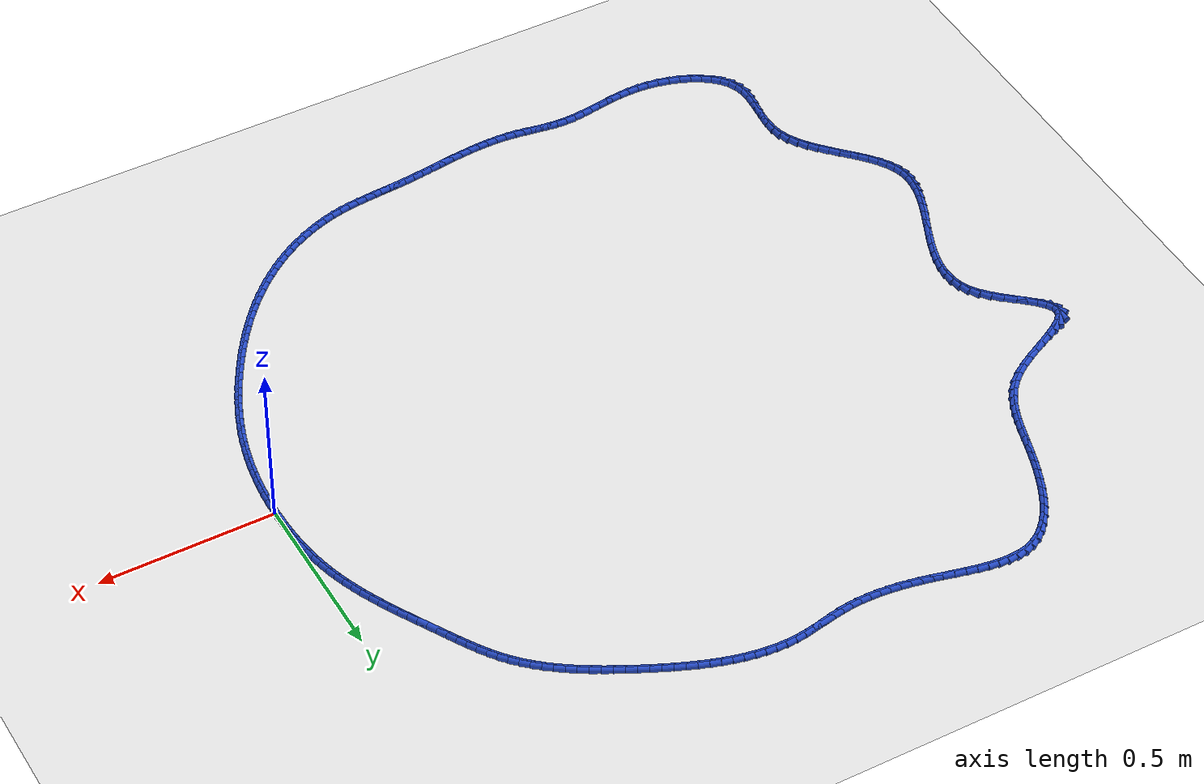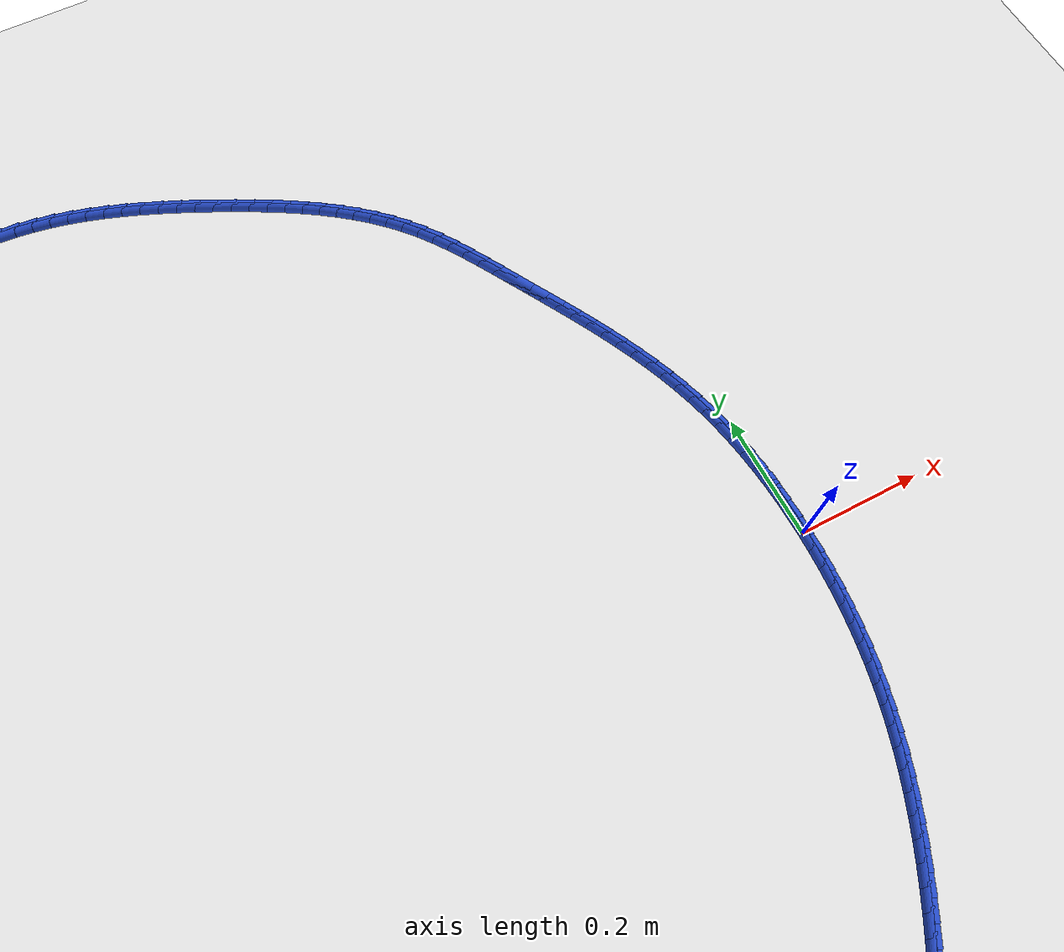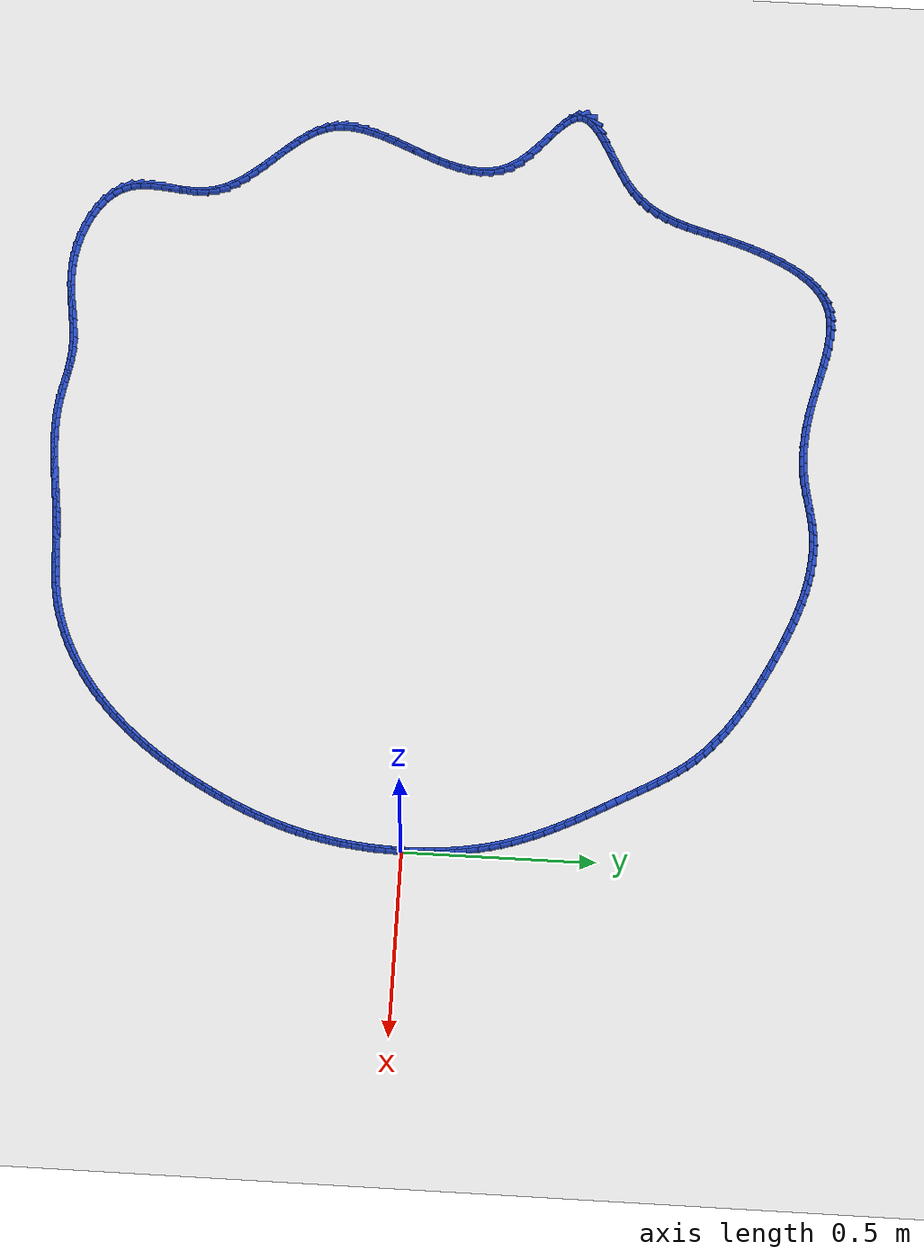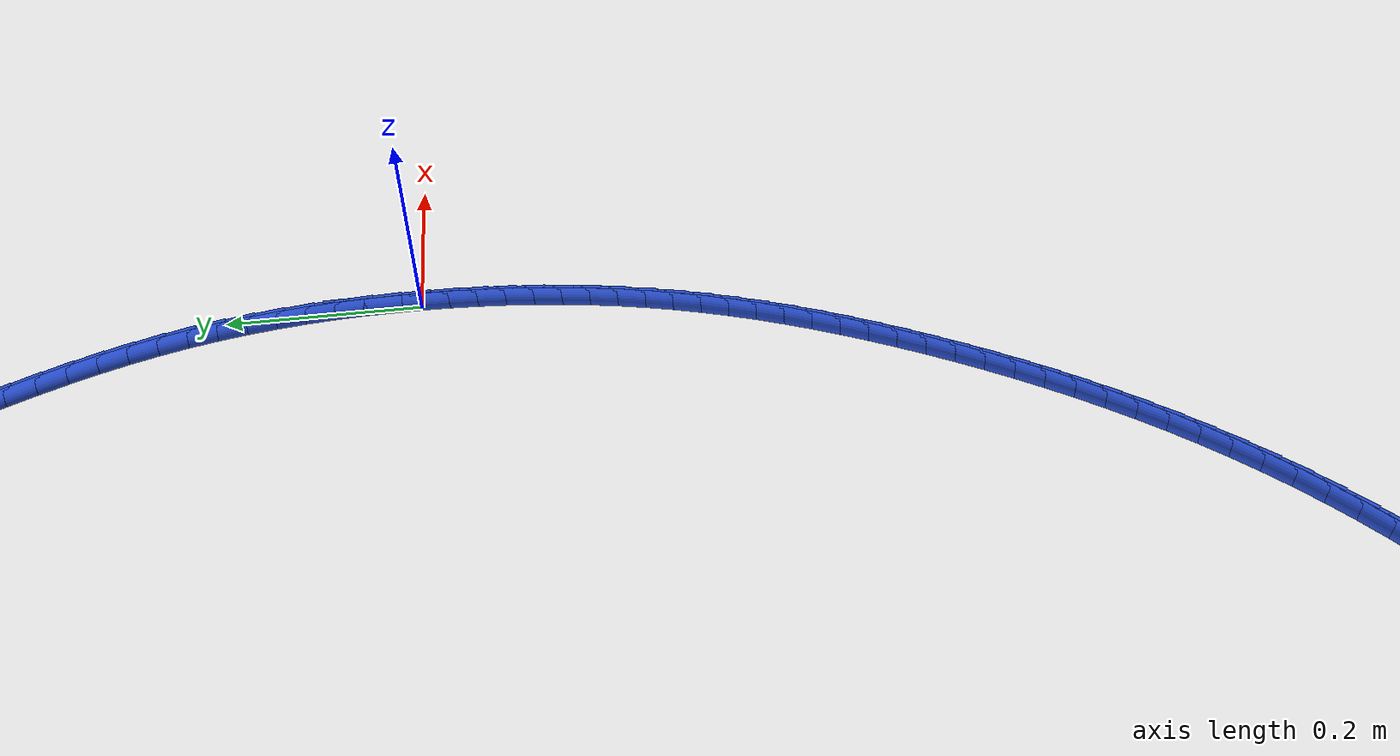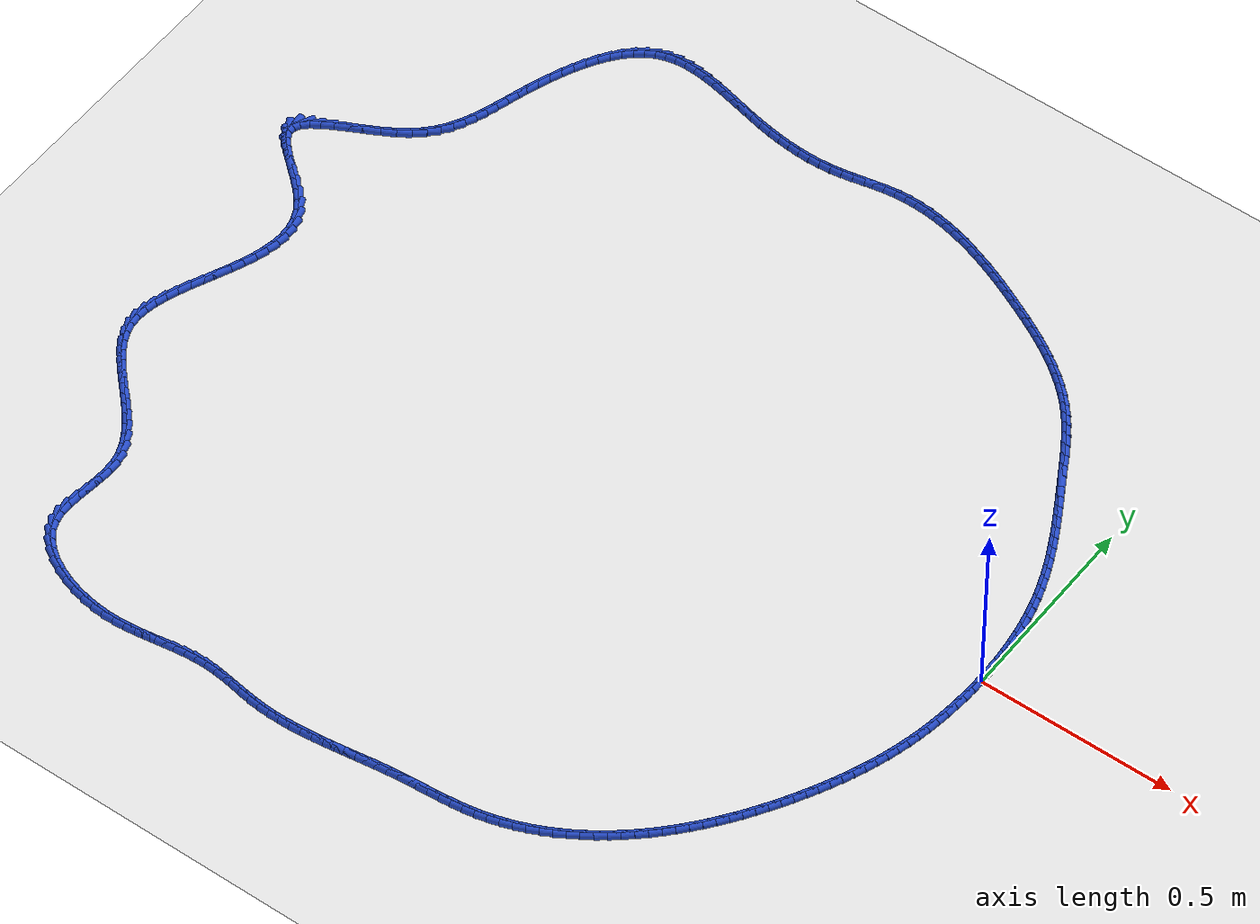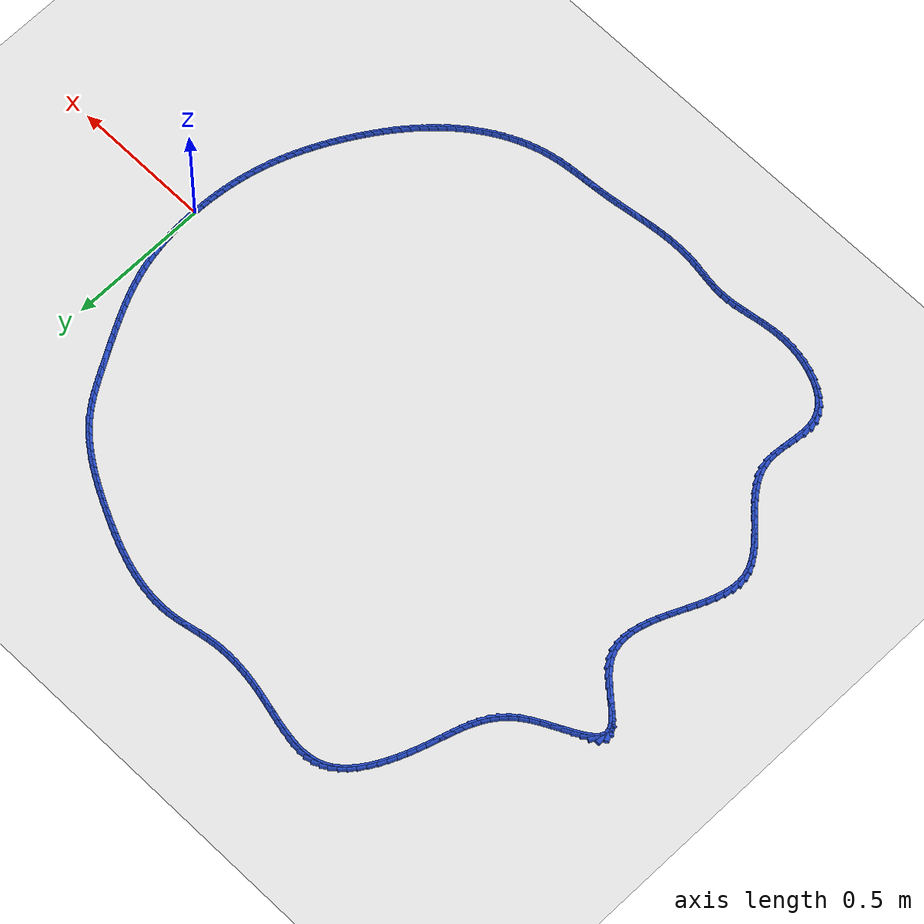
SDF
<sdf version="1.6">
 <world name="default">
  <light name="sun" type="directional">
   <pose>0 0 10 0 -0 0</pose>
   <diffuse>0.8 0.8 0.8 1</diffuse>
   <specular>0.2 0.2 0.2 1</specular>
   <attenuation>
    <range>1000</range>
    <constant>0.9</constant>
    <linear>0.01</linear>
    <quadratic>0.001</quadratic>
   </attenuation>
   <direction>-0.5 0.1 -0.9</direction>
  </light>
  <model name="ground_plane">
   <static>1</static>
   <link name="link">
    <collision name="collision">
     <geometry><plane><normal>0 0 1</normal><size>100 100</size></plane></geometry>
     <surface><friction><ode><mu>100</mu><mu2>50</mu2></ode></friction></surface>
    </collision>
    <visual name="visual">
     <cast_shadows>0</cast_shadows>
     <geometry><plane><normal>0 0 1</normal><size>100 100</size></plane></geometry>
     <material>
      <script><uri>file://media/materials/scripts/gazebo.material</uri><name>Gazebo/WhiteGlow</name></script>
     </material>
    </visual>
   </link>
  </model>
  <gravity>0 0 -9.8</gravity>
  <magnetic_field>6e-06 2.3e-05 -4.2e-05</magnetic_field>
  <atmosphere type="adiabatic"/>
  <physics name="default_physics" default="0" type="ode">
   <max_step_size>0.001</max_step_size>
   <real_time_factor>1</real_time_factor>
   <real_time_update_rate>1000</real_time_update_rate>
  </physics>
  <scene><ambient>0.4 0.4 0.4 1</ambient><background>0.7 0.7 0.7 1</background><shadows>1</shadows></scene>
  <spherical_coordinates>
   <surface_model>EARTH_WGS84</surface_model>
   <latitude_deg>0</latitude_deg>
   <longitude_deg>0</longitude_deg>
   <elevation>0</elevation>
   <heading_deg>0</heading_deg>
  </spherical_coordinates>
  <model name="line">
   <link name="link_0">
    <pose>4.7704895589362195e-18 -6.245004513516506e-17 0.01 0 1.57 -1.5629209023628228</pose>
    <collision name="collision">
     <geometry><cylinder><radius>0.01</radius><length>0.08</length></cylinder></geometry>
    </collision>
    <visual name="visual">
     <material>
      <script><name>Gazebo/Blue</name><uri>file://media/materials/scripts/gazebo.material</uri></script>
     </material>
     <geometry><cylinder><radius>0.01</radius><length>0.08</length></cylinder></geometry>
    </visual>
   </link>
   <link name="link_1">
    <pose>-0.00023221748244270946 0.02948573547209938 0.01 0 1.57 -1.5352980355286454</pose>
    <collision name="collision">
     <geometry><cylinder><radius>0.01</radius><length>0.08</length></cylinder></geometry>
    </collision>
    <visual name="visual">
     <material>
      <script><name>Gazebo/Blue</name><uri>file://media/materials/scripts/gazebo.material</uri></script>
     </material>
     <geometry><cylinder><radius>0.01</radius><length>0.08</length></cylinder></geometry>
    </visual>
   </link>
   <link name="link_2">
    <pose>-0.0012787325749304562 0.058954068651304745 0.01 0 1.57 -1.5062883083713505</pose>
    <collision name="collision">
     <geometry><cylinder><radius>0.01</radius><length>0.08</length></cylinder></geometry>
    </collision>
    <visual name="visual">
     <material>
      <script><name>Gazebo/Blue</name><uri>file://media/materials/scripts/gazebo.material</uri></script>
     </material>
     <geometry><cylinder><radius>0.01</radius><length>0.08</length></cylinder></geometry>
    </visual>
   </link>
   <link name="link_3">
    <pose>-0.003178094569946696 0.08835702839211973 0.01 0 1.57 -1.475801615378492</pose>
    <collision name="collision">
     <geometry><cylinder><radius>0.01</radius><length>0.08</length></cylinder></geometry>
    </collision>
    <visual name="visual">
     <material>
      <script><name>Gazebo/Blue</name><uri>file://media/materials/scripts/gazebo.material</uri></script>
     </material>
     <geometry><cylinder><radius>0.01</radius><length>0.08</length></cylinder></geometry>
    </visual>
   </link>
   <link name="link_4">
    <pose>-0.005968852759974889 0.11764664354904802 0.01 0 1.57 -1.4437493100206276</pose>
    <collision name="collision">
     <geometry><cylinder><radius>0.01</radius><length>0.08</length></cylinder></geometry>
    </collision>
    <visual name="visual">
     <material>
      <script><name>Gazebo/Blue</name><uri>file://media/materials/scripts/gazebo.material</uri></script>
     </material>
     <geometry><cylinder><radius>0.01</radius><length>0.08</length></cylinder></geometry>
    </visual>
   </link>
   <link name="link_5">
    <pose>-0.009689556437498494 0.1467749429765933 0.01 0 1.57 -1.4100460913188793</pose>
    <collision name="collision">
     <geometry><cylinder><radius>0.01</radius><length>0.08</length></cylinder></geometry>
    </collision>
    <visual name="visual">
     <material>
      <script><name>Gazebo/Blue</name><uri>file://media/materials/scripts/gazebo.material</uri></script>
     </material>
     <geometry><cylinder><radius>0.01</radius><length>0.08</length></cylinder></geometry>
    </visual>
   </link>
   <link name="link_6">
    <pose>-0.014378754895000982 0.17569395552925932 0.01 0 1.57 -1.3746124160555075</pose>
    <collision name="collision">
     <geometry><cylinder><radius>0.01</radius><length>0.08</length></cylinder></geometry>
    </collision>
    <visual name="visual">
     <material>
      <script><name>Gazebo/Blue</name><uri>file://media/materials/scripts/gazebo.material</uri></script>
     </material>
     <geometry><cylinder><radius>0.01</radius><length>0.08</length></cylinder></geometry>
    </visual>
   </link>
   <link name="link_7">
    <pose>-0.020074997424965796 0.20435571006154968 0.01 0 1.57 -1.337377485182759</pose>
    <collision name="collision">
     <geometry><cylinder><radius>0.01</radius><length>0.08</length></cylinder></geometry>
    </collision>
    <visual name="visual">
     <material>
      <script><name>Gazebo/Blue</name><uri>file://media/materials/scripts/gazebo.material</uri></script>
     </material>
     <geometry><cylinder><radius>0.01</radius><length>0.08</length></cylinder></geometry>
    </visual>
   </link>
   <link name="link_8">
    <pose>-0.026816833319876405 0.23271223542796812 0.01 0 1.57 -1.298283107460611</pose>
    <collision name="collision">
     <geometry><cylinder><radius>0.01</radius><length>0.08</length></cylinder></geometry>
    </collision>
    <visual name="visual">
     <material>
      <script><name>Gazebo/Blue</name><uri>file://media/materials/scripts/gazebo.material</uri></script>
     </material>
     <geometry><cylinder><radius>0.01</radius><length>0.08</length></cylinder></geometry>
    </visual>
   </link>
   <link name="link_9">
    <pose>-0.03464280465747828 0.260715564975437 0.01 0 1.57 -1.2583799499070445</pose>
    <collision name="collision">
     <geometry><cylinder><radius>0.01</radius><length>0.08</length></cylinder></geometry>
    </collision>
    <visual name="visual">
     <material>
      <script><name>Gazebo/Blue</name><uri>file://media/materials/scripts/gazebo.material</uri></script>
     </material>
     <geometry><cylinder><radius>0.01</radius><length>0.08</length></cylinder></geometry>
    </visual>
   </link>
   <link name="link_10">
    <pose>-0.04356371488244145 0.28833500413423124 0.01 0 1.57 -1.221281673350799</pose>
    <collision name="collision">
     <geometry><cylinder><radius>0.01</radius><length>0.08</length></cylinder></geometry>
    </collision>
    <visual name="visual">
     <material>
      <script><name>Gazebo/Blue</name><uri>file://media/materials/scripts/gazebo.material</uri></script>
     </material>
     <geometry><cylinder><radius>0.01</radius><length>0.08</length></cylinder></geometry>
    </visual>
   </link>
   <link name="link_11">
    <pose>-0.05349984542358672 0.3155962239024136 0.01 0 1.57 -1.1878240595809395</pose>
    <collision name="collision">
     <geometry><cylinder><radius>0.01</radius><length>0.08</length></cylinder></geometry>
    </collision>
    <visual name="visual">
     <material>
      <script><name>Gazebo/Blue</name><uri>file://media/materials/scripts/gazebo.material</uri></script>
     </material>
     <geometry><cylinder><radius>0.01</radius><length>0.08</length></cylinder></geometry>
    </visual>
   </link>
   <link name="link_12">
    <pose>-0.06435304236888054 0.3425363744573921 0.01 0 1.57 -1.158070794779581</pose>
    <collision name="collision">
     <geometry><cylinder><radius>0.01</radius><length>0.08</length></cylinder></geometry>
    </collision>
    <visual name="visual">
     <material>
      <script><name>Gazebo/Blue</name><uri>file://media/materials/scripts/gazebo.material</uri></script>
     </material>
     <geometry><cylinder><radius>0.01</radius><length>0.08</length></cylinder></geometry>
    </visual>
   </link>
   <link name="link_13">
    <pose>-0.07602515180628931 0.3691926059765749 0.01 0 1.57 -1.132042852908517</pose>
    <collision name="collision">
     <geometry><cylinder><radius>0.01</radius><length>0.08</length></cylinder></geometry>
    </collision>
    <visual name="visual">
     <material>
      <script><name>Gazebo/Blue</name><uri>file://media/materials/scripts/gazebo.material</uri></script>
     </material>
     <geometry><cylinder><radius>0.01</radius><length>0.08</length></cylinder></geometry>
    </visual>
   </link>
   <link name="link_14">
    <pose>-0.08841801982377952 0.3956020686373699 0.01 0 1.57 -1.1097306610585636</pose>
    <collision name="collision">
     <geometry><cylinder><radius>0.01</radius><length>0.08</length></cylinder></geometry>
    </collision>
    <visual name="visual">
     <material>
      <script><name>Gazebo/Blue</name><uri>file://media/materials/scripts/gazebo.material</uri></script>
     </material>
     <geometry><cylinder><radius>0.01</radius><length>0.08</length></cylinder></geometry>
    </visual>
   </link>
   <link name="link_15">
    <pose>-0.10143349250931759 0.4218019126171854 0.01 0 1.57 -1.091105020452687</pose>
    <collision name="collision">
     <geometry><cylinder><radius>0.01</radius><length>0.08</length></cylinder></geometry>
    </collision>
    <visual name="visual">
     <material>
      <script><name>Gazebo/Blue</name><uri>file://media/materials/scripts/gazebo.material</uri></script>
     </material>
     <geometry><cylinder><radius>0.01</radius><length>0.08</length></cylinder></geometry>
    </visual>
   </link>
   <link name="link_16">
    <pose>-0.11497341595087 0.4478292880934293 0.01 0 1.57 -1.076126383886536</pose>
    <collision name="collision">
     <geometry><cylinder><radius>0.01</radius><length>0.08</length></cylinder></geometry>
    </collision>
    <visual name="visual">
     <material>
      <script><name>Gazebo/Blue</name><uri>file://media/materials/scripts/gazebo.material</uri></script>
     </material>
     <geometry><cylinder><radius>0.01</radius><length>0.08</length></cylinder></geometry>
    </visual>
   </link>
   <link name="link_17">
    <pose>-0.12893963623640314 0.4737213452435097 0.01 0 1.57 -1.0647523619161336</pose>
    <collision name="collision">
     <geometry><cylinder><radius>0.01</radius><length>0.08</length></cylinder></geometry>
    </collision>
    <visual name="visual">
     <material>
      <script><name>Gazebo/Blue</name><uri>file://media/materials/scripts/gazebo.material</uri></script>
     </material>
     <geometry><cylinder><radius>0.01</radius><length>0.08</length></cylinder></geometry>
    </visual>
   </link>
   <link name="link_18">
    <pose>-0.14323399945388351 0.49951523424483457 0.01 0 1.57 -1.0569435000491039</pose>
    <collision name="collision">
     <geometry><cylinder><radius>0.01</radius><length>0.08</length></cylinder></geometry>
    </collision>
    <visual name="visual">
     <material>
      <script><name>Gazebo/Blue</name><uri>file://media/materials/scripts/gazebo.material</uri></script>
     </material>
     <geometry><cylinder><radius>0.01</radius><length>0.08</length></cylinder></geometry>
    </visual>
   </link>
   <link name="link_19">
    <pose>-0.15775835169127758 0.5252481052748124 0.01 0 1.57 -1.0526674543015924</pose>
    <collision name="collision">
     <geometry><cylinder><radius>0.01</radius><length>0.08</length></cylinder></geometry>
    </collision>
    <visual name="visual">
     <material>
      <script><name>Gazebo/Blue</name><uri>file://media/materials/scripts/gazebo.material</uri></script>
     </material>
     <geometry><cylinder><radius>0.01</radius><length>0.08</length></cylinder></geometry>
    </visual>
   </link>
   <link name="link_20">
    <pose>-0.17241453903655168 0.5509571085108506 0.01 0 1.57 -1.051888246477109</pose>
    <collision name="collision">
     <geometry><cylinder><radius>0.01</radius><length>0.08</length></cylinder></geometry>
    </collision>
    <visual name="visual">
     <material>
      <script><name>Gazebo/Blue</name><uri>file://media/materials/scripts/gazebo.material</uri></script>
     </material>
     <geometry><cylinder><radius>0.01</radius><length>0.08</length></cylinder></geometry>
    </visual>
   </link>
   <link name="link_21">
    <pose>-0.18710472720954635 0.5766791493343209 0.01 0 1.57 -1.0512040113902683</pose>
    <collision name="collision">
     <geometry><cylinder><radius>0.01</radius><length>0.08</length></cylinder></geometry>
    </collision>
    <visual name="visual">
     <material>
      <script><name>Gazebo/Blue</name><uri>file://media/materials/scripts/gazebo.material</uri></script>
     </material>
     <geometry><cylinder><radius>0.01</radius><length>0.08</length></cylinder></geometry>
    </visual>
   </link>
   <link name="link_22">
    <pose>-0.20181157151103613 0.602389488678617 0.01 0 1.57 -1.0427449161024778</pose>
    <collision name="collision">
     <geometry><cylinder><radius>0.01</radius><length>0.08</length></cylinder></geometry>
    </collision>
    <visual name="visual">
     <material>
      <script><name>Gazebo/Blue</name><uri>file://media/materials/scripts/gazebo.material</uri></script>
     </material>
     <geometry><cylinder><radius>0.01</radius><length>0.08</length></cylinder></geometry>
    </visual>
   </link>
   <link name="link_23">
    <pose>-0.21670400383865696 0.6279207240683891 0.01 0 1.57 -1.0252946663096587</pose>
    <collision name="collision">
     <geometry><cylinder><radius>0.01</radius><length>0.08</length></cylinder></geometry>
    </collision>
    <visual name="visual">
     <material>
      <script><name>Gazebo/Blue</name><uri>file://media/materials/scripts/gazebo.material</uri></script>
     </material>
     <geometry><cylinder><radius>0.01</radius><length>0.08</length></cylinder></geometry>
    </visual>
   </link>
   <link name="link_24">
    <pose>-0.23197723167758644 0.6530853293791075 0.01 0 1.57 -0.9986476846632024</pose>
    <collision name="collision">
     <geometry><cylinder><radius>0.01</radius><length>0.08</length></cylinder></geometry>
    </collision>
    <visual name="visual">
     <material>
      <script><name>Gazebo/Blue</name><uri>file://media/materials/scripts/gazebo.material</uri></script>
     </material>
     <geometry><cylinder><radius>0.01</radius><length>0.08</length></cylinder></geometry>
    </visual>
   </link>
   <link name="link_25">
    <pose>-0.24782646251300203 0.677695778486243 0.01 0 1.57 -0.9625404371289182</pose>
    <collision name="collision">
     <geometry><cylinder><radius>0.01</radius><length>0.08</length></cylinder></geometry>
    </collision>
    <visual name="visual">
     <material>
      <script><name>Gazebo/Blue</name><uri>file://media/materials/scripts/gazebo.material</uri></script>
     </material>
     <geometry><cylinder><radius>0.01</radius><length>0.08</length></cylinder></geometry>
    </visual>
   </link>
   <link name="link_26">
    <pose>-0.26444690383008135 0.7015645452652665 0.01 0 1.57 -0.9167173207357576</pose>
    <collision name="collision">
     <geometry><cylinder><radius>0.01</radius><length>0.08</length></cylinder></geometry>
    </collision>
    <visual name="visual">
     <material>
      <script><name>Gazebo/Blue</name><uri>file://media/materials/scripts/gazebo.material</uri></script>
     </material>
     <geometry><cylinder><radius>0.01</radius><length>0.08</length></cylinder></geometry>
    </visual>
   </link>
   <link name="link_27">
    <pose>-0.2820337631140019 0.7245041035916483 0.01 0 1.57 -0.8611853308796491</pose>
    <collision name="collision">
     <geometry><cylinder><radius>0.01</radius><length>0.08</length></cylinder></geometry>
    </collision>
    <visual name="visual">
     <material>
      <script><name>Gazebo/Blue</name><uri>file://media/materials/scripts/gazebo.material</uri></script>
     </material>
     <geometry><cylinder><radius>0.01</radius><length>0.08</length></cylinder></geometry>
    </visual>
   </link>
   <link name="link_28">
    <pose>-0.3007789875294239 0.7463299986361427 0.01 0 1.57 -0.8018477974935236</pose>
    <collision name="collision">
     <geometry><cylinder><radius>0.01</radius><length>0.08</length></cylinder></geometry>
    </collision>
    <visual name="visual">
     <material>
      <script><name>Gazebo/Blue</name><uri>file://media/materials/scripts/gazebo.material</uri></script>
     </material>
     <geometry><cylinder><radius>0.01</radius><length>0.08</length></cylinder></geometry>
    </visual>
   </link>
   <link name="link_29">
    <pose>-0.32075303088894985 0.7669722250407089 0.01 0 1.57 -0.7464528965106183</pose>
    <collision name="collision">
     <geometry><cylinder><radius>0.01</radius><length>0.08</length></cylinder></geometry>
    </collision>
    <visual name="visual">
     <material>
      <script><name>Gazebo/Blue</name><uri>file://media/materials/scripts/gazebo.material</uri></script>
     </material>
     <geometry><cylinder><radius>0.01</radius><length>0.08</length></cylinder></geometry>
    </visual>
   </link>
   <link name="link_30">
    <pose>-0.3418714955043365 0.786506651045218 0.01 0 1.57 -0.6957562835783553</pose>
    <collision name="collision">
     <geometry><cylinder><radius>0.01</radius><length>0.08</length></cylinder></geometry>
    </collision>
    <visual name="visual">
     <material>
      <script><name>Gazebo/Blue</name><uri>file://media/materials/scripts/gazebo.material</uri></script>
     </material>
     <geometry><cylinder><radius>0.01</radius><length>0.08</length></cylinder></geometry>
    </visual>
   </link>
   <link name="link_31">
    <pose>-0.3640399283989551 0.8050186171974407 0.01 0 1.57 -0.6498881633122606</pose>
    <collision name="collision">
     <geometry><cylinder><radius>0.01</radius><length>0.08</length></cylinder></geometry>
    </collision>
    <visual name="visual">
     <material>
      <script><name>Gazebo/Blue</name><uri>file://media/materials/scripts/gazebo.material</uri></script>
     </material>
     <geometry><cylinder><radius>0.01</radius><length>0.08</length></cylinder></geometry>
    </visual>
   </link>
   <link name="link_32">
    <pose>-0.3871638765961772 0.8225934640451474 0.01 0 1.57 -0.6088644613753241</pose>
    <collision name="collision">
     <geometry><cylinder><radius>0.01</radius><length>0.08</length></cylinder></geometry>
    </collision>
    <visual name="visual">
     <material>
      <script><name>Gazebo/Blue</name><uri>file://media/materials/scripts/gazebo.material</uri></script>
     </material>
     <geometry><cylinder><radius>0.01</radius><length>0.08</length></cylinder></geometry>
    </visual>
   </link>
   <link name="link_33">
    <pose>-0.4111488871193742 0.8393165321361098 0.01 0 1.57 -0.5726192543472648</pose>
    <collision name="collision">
     <geometry><cylinder><radius>0.01</radius><length>0.08</length></cylinder></geometry>
    </collision>
    <visual name="visual">
     <material>
      <script><name>Gazebo/Blue</name><uri>file://media/materials/scripts/gazebo.material</uri></script>
     </material>
     <geometry><cylinder><radius>0.01</radius><length>0.08</length></cylinder></geometry>
    </visual>
   </link>
   <link name="link_34">
    <pose>-0.4359005069919173 0.8552731620180979 0.01 0 1.57 -0.5410343319276107</pose>
    <collision name="collision">
     <geometry><cylinder><radius>0.01</radius><length>0.08</length></cylinder></geometry>
    </collision>
    <visual name="visual">
     <material>
      <script><name>Gazebo/Blue</name><uri>file://media/materials/scripts/gazebo.material</uri></script>
     </material>
     <geometry><cylinder><radius>0.01</radius><length>0.08</length></cylinder></geometry>
    </visual>
   </link>
   <link name="link_35">
    <pose>-0.4613242832371782 0.8705486942388833 0.01 0 1.57 -0.5139640245349182</pose>
    <collision name="collision">
     <geometry><cylinder><radius>0.01</radius><length>0.08</length></cylinder></geometry>
    </collision>
    <visual name="visual">
     <material>
      <script><name>Gazebo/Blue</name><uri>file://media/materials/scripts/gazebo.material</uri></script>
     </material>
     <geometry><cylinder><radius>0.01</radius><length>0.08</length></cylinder></geometry>
    </visual>
   </link>
   <link name="link_36">
    <pose>-0.4873257628785281 0.8852284693462363 0.01 0 1.57 -0.49125482677589577</pose>
    <collision name="collision">
     <geometry><cylinder><radius>0.01</radius><length>0.08</length></cylinder></geometry>
    </collision>
    <visual name="visual">
     <material>
      <script><name>Gazebo/Blue</name><uri>file://media/materials/scripts/gazebo.material</uri></script>
     </material>
     <geometry><cylinder><radius>0.01</radius><length>0.08</length></cylinder></geometry>
    </visual>
   </link>
   <link name="link_37">
    <pose>-0.5138104929393388 0.8993978278879287 0.01 0 1.57 -0.47276019355298965</pose>
    <collision name="collision">
     <geometry><cylinder><radius>0.01</radius><length>0.08</length></cylinder></geometry>
    </collision>
    <visual name="visual">
     <material>
      <script><name>Gazebo/Blue</name><uri>file://media/materials/scripts/gazebo.material</uri></script>
     </material>
     <geometry><cylinder><radius>0.01</radius><length>0.08</length></cylinder></geometry>
    </visual>
   </link>
   <link name="link_38">
    <pose>-0.540684020442981 0.9131421104117302 0.01 0 1.57 -0.4583430941588678</pose>
    <collision name="collision">
     <geometry><cylinder><radius>0.01</radius><length>0.08</length></cylinder></geometry>
    </collision>
    <visual name="visual">
     <material>
      <script><name>Gazebo/Blue</name><uri>file://media/materials/scripts/gazebo.material</uri></script>
     </material>
     <geometry><cylinder><radius>0.01</radius><length>0.08</length></cylinder></geometry>
    </visual>
   </link>
   <link name="link_39">
    <pose>-0.5678519825734893 0.9265464252400162 0.01 0 1.57 -0.44590105547631476</pose>
    <collision name="collision">
     <geometry><cylinder><radius>0.01</radius><length>0.08</length></cylinder></geometry>
    </collision>
    <visual name="visual">
     <material>
      <script><name>Gazebo/Blue</name><uri>file://media/materials/scripts/gazebo.material</uri></script>
     </material>
     <geometry><cylinder><radius>0.01</radius><length>0.08</length></cylinder></geometry>
    </visual>
   </link>
   <link name="link_40">
    <pose>-0.5952420461567419 0.9396391392941753 0.01 0 1.57 -0.4307602638622326</pose>
    <collision name="collision">
     <geometry><cylinder><radius>0.01</radius><length>0.08</length></cylinder></geometry>
    </collision>
    <visual name="visual">
     <material>
      <script><name>Gazebo/Blue</name><uri>file://media/materials/scripts/gazebo.material</uri></script>
     </material>
     <geometry><cylinder><radius>0.01</radius><length>0.08</length></cylinder></geometry>
    </visual>
   </link>
   <link name="link_41">
    <pose>-0.6228325444586533 0.9523181187452506 0.01 0 1.57 -0.412189025677803</pose>
    <collision name="collision">
     <geometry><cylinder><radius>0.01</radius><length>0.08</length></cylinder></geometry>
    </collision>
    <visual name="visual">
     <material>
      <script><name>Gazebo/Blue</name><uri>file://media/materials/scripts/gazebo.material</uri></script>
     </material>
     <geometry><cylinder><radius>0.01</radius><length>0.08</length></cylinder></geometry>
    </visual>
   </link>
   <link name="link_42">
    <pose>-0.6506089074274387 0.9644629509516289 0.01 0 1.57 -0.39006887813816987</pose>
    <collision name="collision">
     <geometry><cylinder><radius>0.01</radius><length>0.08</length></cylinder></geometry>
    </collision>
    <visual name="visual">
     <material>
      <script><name>Gazebo/Blue</name><uri>file://media/materials/scripts/gazebo.material</uri></script>
     </material>
     <geometry><cylinder><radius>0.01</radius><length>0.08</length></cylinder></geometry>
    </visual>
   </link>
   <link name="link_43">
    <pose>-0.6785565650113139 0.9759532232716974 0.01 0 1.57 -0.3642544920603681</pose>
    <collision name="collision">
     <geometry><cylinder><radius>0.01</radius><length>0.08</length></cylinder></geometry>
    </collision>
    <visual name="visual">
     <material>
      <script><name>Gazebo/Blue</name><uri>file://media/materials/scripts/gazebo.material</uri></script>
     </material>
     <geometry><cylinder><radius>0.01</radius><length>0.08</length></cylinder></geometry>
    </visual>
   </link>
   <link name="link_44">
    <pose>-0.7066609471584948 0.9866685230638432 0.01 0 1.57 -0.33457994045460715</pose>
    <collision name="collision">
     <geometry><cylinder><radius>0.01</radius><length>0.08</length></cylinder></geometry>
    </collision>
    <visual name="visual">
     <material>
      <script><name>Gazebo/Blue</name><uri>file://media/materials/scripts/gazebo.material</uri></script>
     </material>
     <geometry><cylinder><radius>0.01</radius><length>0.08</length></cylinder></geometry>
    </visual>
   </link>
   <link name="link_45">
    <pose>-0.7349074838171972 0.9964884376864537 0.01 0 1.57 -0.30086735414312865</pose>
    <collision name="collision">
     <geometry><cylinder><radius>0.01</radius><length>0.08</length></cylinder></geometry>
    </collision>
    <visual name="visual">
     <material>
      <script><name>Gazebo/Blue</name><uri>file://media/materials/scripts/gazebo.material</uri></script>
     </material>
     <geometry><cylinder><radius>0.01</radius><length>0.08</length></cylinder></geometry>
    </visual>
   </link>
   <link name="link_46">
    <pose>-0.7632816049356363 1.0052925544979157 0.01 0 1.57 -0.2629388572317301</pose>
    <collision name="collision">
     <geometry><cylinder><radius>0.01</radius><length>0.08</length></cylinder></geometry>
    </collision>
    <visual name="visual">
     <material>
      <script><name>Gazebo/Blue</name><uri>file://media/materials/scripts/gazebo.material</uri></script>
     </material>
     <geometry><cylinder><radius>0.01</radius><length>0.08</length></cylinder></geometry>
    </visual>
   </link>
   <link name="link_47">
    <pose>-0.7917687404620288 1.0129604608566165 0.01 0 1.57 -0.22063267449083634</pose>
    <collision name="collision">
     <geometry><cylinder><radius>0.01</radius><length>0.08</length></cylinder></geometry>
    </collision>
    <visual name="visual">
     <material>
      <script><name>Gazebo/Blue</name><uri>file://media/materials/scripts/gazebo.material</uri></script>
     </material>
     <geometry><cylinder><radius>0.01</radius><length>0.08</length></cylinder></geometry>
    </visual>
   </link>
   <link name="link_48">
    <pose>-0.8203543203445897 1.019371744120943 0.01 0 1.57 -0.17382410248840413</pose>
    <collision name="collision">
     <geometry><cylinder><radius>0.01</radius><length>0.08</length></cylinder></geometry>
    </collision>
    <visual name="visual">
     <material>
      <script><name>Gazebo/Blue</name><uri>file://media/materials/scripts/gazebo.material</uri></script>
     </material>
     <geometry><cylinder><radius>0.01</radius><length>0.08</length></cylinder></geometry>
    </visual>
   </link>
   <link name="link_49">
    <pose>-0.8490237745315345 1.0244059916492823 0.01 0 1.57 -0.12245150060278656</pose>
    <collision name="collision">
     <geometry><cylinder><radius>0.01</radius><length>0.08</length></cylinder></geometry>
    </collision>
    <visual name="visual">
     <material>
      <script><name>Gazebo/Blue</name><uri>file://media/materials/scripts/gazebo.material</uri></script>
     </material>
     <geometry><cylinder><radius>0.01</radius><length>0.08</length></cylinder></geometry>
    </visual>
   </link>
   <link name="link_50">
    <pose>-0.8777625329710799 1.0279427908000218 0.01 0 1.57 -0.06654644822876513</pose>
    <collision name="collision">
     <geometry><cylinder><radius>0.01</radius><length>0.08</length></cylinder></geometry>
    </collision>
    <visual name="visual">
     <material>
      <script><name>Gazebo/Blue</name><uri>file://media/materials/scripts/gazebo.material</uri></script>
     </material>
     <geometry><cylinder><radius>0.01</radius><length>0.08</length></cylinder></geometry>
    </visual>
   </link>
   <link name="link_51">
    <pose>-0.9065560256114404 1.0298617289315486 0.01 0 1.57 -0.0062656675080587166</pose>
    <collision name="collision">
     <geometry><cylinder><radius>0.01</radius><length>0.08</length></cylinder></geometry>
    </collision>
    <visual name="visual">
     <material>
      <script><name>Gazebo/Blue</name><uri>file://media/materials/scripts/gazebo.material</uri></script>
     </material>
     <geometry><cylinder><radius>0.01</radius><length>0.08</length></cylinder></geometry>
    </visual>
   </link>
   <link name="link_52">
    <pose>-0.9353896824008328 1.0300423934022493 0.01 0 1.57 0.058079630058301544</pose>
    <collision name="collision">
     <geometry><cylinder><radius>0.01</radius><length>0.08</length></cylinder></geometry>
    </collision>
    <visual name="visual">
     <material>
      <script><name>Gazebo/Blue</name><uri>file://media/materials/scripts/gazebo.material</uri></script>
     </material>
     <geometry><cylinder><radius>0.01</radius><length>0.08</length></cylinder></geometry>
    </visual>
   </link>
   <link name="link_53">
    <pose>-0.964248933287472 1.0283643715705115 0.01 0 1.57 0.12253561640505588</pose>
    <collision name="collision">
     <geometry><cylinder><radius>0.01</radius><length>0.08</length></cylinder></geometry>
    </collision>
    <visual name="visual">
     <material>
      <script><name>Gazebo/Blue</name><uri>file://media/materials/scripts/gazebo.material</uri></script>
     </material>
     <geometry><cylinder><radius>0.01</radius><length>0.08</length></cylinder></geometry>
    </visual>
   </link>
   <link name="link_54">
    <pose>-0.9931190645048581 1.0248089394972961 0.01 0 1.57 0.1687357305586583</pose>
    <collision name="collision">
     <geometry><cylinder><radius>0.01</radius><length>0.08</length></cylinder></geometry>
    </collision>
    <visual name="visual">
     <material>
      <script><name>Gazebo/Blue</name><uri>file://media/materials/scripts/gazebo.material</uri></script>
     </material>
     <geometry><cylinder><radius>0.01</radius><length>0.08</length></cylinder></geometry>
    </visual>
   </link>
   <link name="link_55">
    <pose>-1.0219846073684027 1.0198915331607437 0.01 0 1.57 0.19139211059573905</pose>
    <collision name="collision">
     <geometry><cylinder><radius>0.01</radius><length>0.08</length></cylinder></geometry>
    </collision>
    <visual name="visual">
     <material>
      <script><name>Gazebo/Blue</name><uri>file://media/materials/scripts/gazebo.material</uri></script>
     </material>
     <geometry><cylinder><radius>0.01</radius><length>0.08</length></cylinder></geometry>
    </visual>
   </link>
   <link name="link_56">
    <pose>-1.0508298461791241 1.014302369339393 0.01 0 1.57 0.19100467956801448</pose>
    <collision name="collision">
     <geometry><cylinder><radius>0.01</radius><length>0.08</length></cylinder></geometry>
    </collision>
    <visual name="visual">
     <material>
      <script><name>Gazebo/Blue</name><uri>file://media/materials/scripts/gazebo.material</uri></script>
     </material>
     <geometry><cylinder><radius>0.01</radius><length>0.08</length></cylinder></geometry>
    </visual>
   </link>
   <link name="link_57">
    <pose>-1.0796390650969527 1.008731764642111 0.01 0 1.57 0.16747604173135128</pose>
    <collision name="collision">
     <geometry><cylinder><radius>0.01</radius><length>0.08</length></cylinder></geometry>
    </collision>
    <visual name="visual">
     <material>
      <script><name>Gazebo/Blue</name><uri>file://media/materials/scripts/gazebo.material</uri></script>
     </material>
     <geometry><cylinder><radius>0.01</radius><length>0.08</length></cylinder></geometry>
    </visual>
   </link>
   <link name="link_58">
    <pose>-1.1083965482818192 1.0038700356777632 0.01 0 1.57 0.12100863812179356</pose>
    <collision name="collision">
     <geometry><cylinder><radius>0.01</radius><length>0.08</length></cylinder></geometry>
    </collision>
    <visual name="visual">
     <material>
      <script><name>Gazebo/Blue</name><uri>file://media/materials/scripts/gazebo.material</uri></script>
     </material>
     <geometry><cylinder><radius>0.01</radius><length>0.08</length></cylinder></geometry>
    </visual>
   </link>
   <link name="link_59">
    <pose>-1.1370893118881078 1.0003809162843078 0.01 0 1.57 0.0652808433842499</pose>
    <collision name="collision">
     <geometry><cylinder><radius>0.01</radius><length>0.08</length></cylinder></geometry>
    </collision>
    <visual name="visual">
     <material>
      <script><name>Gazebo/Blue</name><uri>file://media/materials/scripts/gazebo.material</uri></script>
     </material>
     <geometry><cylinder><radius>0.01</radius><length>0.08</length></cylinder></geometry>
    </visual>
   </link>
   <link name="link_60">
    <pose>-1.1657476111992182 0.9985074162167823 0.01 0 1.57 0.012231027606359678</pose>
    <collision name="collision">
     <geometry><cylinder><radius>0.01</radius><length>0.08</length></cylinder></geometry>
    </collision>
    <visual name="visual">
     <material>
      <script><name>Gazebo/Blue</name><uri>file://media/materials/scripts/gazebo.material</uri></script>
     </material>
     <geometry><cylinder><radius>0.01</radius><length>0.08</length></cylinder></geometry>
    </visual>
   </link>
   <link name="link_61">
    <pose>-1.1944362371626414 0.9981565073420344 0.01 0 1.57 -0.03713033663335703</pose>
    <collision name="collision">
     <geometry><cylinder><radius>0.01</radius><length>0.08</length></cylinder></geometry>
    </collision>
    <visual name="visual">
     <material>
      <script><name>Gazebo/Blue</name><uri>file://media/materials/scripts/gazebo.material</uri></script>
     </material>
     <geometry><cylinder><radius>0.01</radius><length>0.08</length></cylinder></geometry>
    </visual>
   </link>
   <link name="link_62">
    <pose>-1.223220944417014 0.9992257846480789 0.01 0 1.57 -0.08227820049955427</pose>
    <collision name="collision">
     <geometry><cylinder><radius>0.01</radius><length>0.08</length></cylinder></geometry>
    </collision>
    <visual name="visual">
     <material>
      <script><name>Gazebo/Blue</name><uri>file://media/materials/scripts/gazebo.material</uri></script>
     </material>
     <geometry><cylinder><radius>0.01</radius><length>0.08</length></cylinder></geometry>
    </visual>
   </link>
   <link name="link_63">
    <pose>-1.2521674876009719 1.0016128431229303 0.01 0 1.57 -0.12285852551211134</pose>
    <collision name="collision">
     <geometry><cylinder><radius>0.01</radius><length>0.08</length></cylinder></geometry>
    </collision>
    <visual name="visual">
     <material>
      <script><name>Gazebo/Blue</name><uri>file://media/materials/scripts/gazebo.material</uri></script>
     </material>
     <geometry><cylinder><radius>0.01</radius><length>0.08</length></cylinder></geometry>
    </visual>
   </link>
   <link name="link_64">
    <pose>-1.2813416213531508 1.0052152777546026 0.01 0 1.57 -0.15867541784099093</pose>
    <collision name="collision">
     <geometry><cylinder><radius>0.01</radius><length>0.08</length></cylinder></geometry>
    </collision>
    <visual name="visual">
     <material>
      <script><name>Gazebo/Blue</name><uri>file://media/materials/scripts/gazebo.material</uri></script>
     </material>
     <geometry><cylinder><radius>0.01</radius><length>0.08</length></cylinder></geometry>
    </visual>
   </link>
   <link name="link_65">
    <pose>-1.310809100312188 1.0099306835311106 0.01 0 1.57 -0.1896679077770963</pose>
    <collision name="collision">
     <geometry><cylinder><radius>0.01</radius><length>0.08</length></cylinder></geometry>
    </collision>
    <visual name="visual">
     <material>
      <script><name>Gazebo/Blue</name><uri>file://media/materials/scripts/gazebo.material</uri></script>
     </material>
     <geometry><cylinder><radius>0.01</radius><length>0.08</length></cylinder></geometry>
    </visual>
   </link>
   <link name="link_66">
    <pose>-1.3406356791167195 1.0156566554404687 0.01 0 1.57 -0.21584274983676272</pose>
    <collision name="collision">
     <geometry><cylinder><radius>0.01</radius><length>0.08</length></cylinder></geometry>
    </collision>
    <visual name="visual">
     <material>
      <script><name>Gazebo/Blue</name><uri>file://media/materials/scripts/gazebo.material</uri></script>
     </material>
     <geometry><cylinder><radius>0.01</radius><length>0.08</length></cylinder></geometry>
    </visual>
   </link>
   <link name="link_67">
    <pose>-1.3708860448236102 1.0222892996389903 0.01 0 1.57 -0.2339169108895091</pose>
    <collision name="collision">
     <geometry><cylinder><radius>0.01</radius><length>0.08</length></cylinder></geometry>
    </collision>
    <visual name="visual">
     <material>
      <script><name>Gazebo/Blue</name><uri>file://media/materials/scripts/gazebo.material</uri></script>
     </material>
     <geometry><cylinder><radius>0.01</radius><length>0.08</length></cylinder></geometry>
    </visual>
   </link>
   <link name="link_68">
    <pose>-1.4015288820358027 1.0295908388647284 0.01 0 1.57 -0.2384395150574937</pose>
    <collision name="collision">
     <geometry><cylinder><radius>0.01</radius><length>0.08</length></cylinder></geometry>
    </collision>
    <visual name="visual">
     <material>
      <script><name>Gazebo/Blue</name><uri>file://media/materials/scripts/gazebo.material</uri></script>
     </material>
     <geometry><cylinder><radius>0.01</radius><length>0.08</length></cylinder></geometry>
    </visual>
   </link>
   <link name="link_69">
    <pose>-1.4323620393331582 1.0370852507922248 0.01 0 1.57 -0.22920633937969095</pose>
    <collision name="collision">
     <geometry><cylinder><radius>0.01</radius><length>0.08</length></cylinder></geometry>
    </collision>
    <visual name="visual">
     <material>
      <script><name>Gazebo/Blue</name><uri>file://media/materials/scripts/gazebo.material</uri></script>
     </material>
     <geometry><cylinder><radius>0.01</radius><length>0.08</length></cylinder></geometry>
    </visual>
   </link>
   <link name="link_70">
    <pose>-1.46316575419938 1.0442719529555609 0.01 0 1.57 -0.20579958243474825</pose>
    <collision name="collision">
     <geometry><cylinder><radius>0.01</radius><length>0.08</length></cylinder></geometry>
    </collision>
    <visual name="visual">
     <material>
      <script><name>Gazebo/Blue</name><uri>file://media/materials/scripts/gazebo.material</uri></script>
     </material>
     <geometry><cylinder><radius>0.01</radius><length>0.08</length></cylinder></geometry>
    </visual>
   </link>
   <link name="link_71">
    <pose>-1.4937202641181708 1.050650362888817 0.01 0 1.57 -0.16693585075877002</pose>
    <collision name="collision">
     <geometry><cylinder><radius>0.01</radius><length>0.08</length></cylinder></geometry>
    </collision>
    <visual name="visual">
     <material>
      <script><name>Gazebo/Blue</name><uri>file://media/materials/scripts/gazebo.material</uri></script>
     </material>
     <geometry><cylinder><radius>0.01</radius><length>0.08</length></cylinder></geometry>
    </visual>
   </link>
   <link name="link_72">
    <pose>-1.5238058065732336 1.0557198981260738 0.01 0 1.57 -0.11044772445995889</pose>
    <collision name="collision">
     <geometry><cylinder><radius>0.01</radius><length>0.08</length></cylinder></geometry>
    </collision>
    <visual name="visual">
     <material>
      <script><name>Gazebo/Blue</name><uri>file://media/materials/scripts/gazebo.material</uri></script>
     </material>
     <geometry><cylinder><radius>0.01</radius><length>0.08</length></cylinder></geometry>
    </visual>
   </link>
   <link name="link_73">
    <pose>-1.5532026190482722 1.0589799762014127 0.01 0 1.57 -0.033335995237484345</pose>
    <collision name="collision">
     <geometry><cylinder><radius>0.01</radius><length>0.08</length></cylinder></geometry>
    </collision>
    <visual name="visual">
     <material>
      <script><name>Gazebo/Blue</name><uri>file://media/materials/scripts/gazebo.material</uri></script>
     </material>
     <geometry><cylinder><radius>0.01</radius><length>0.08</length></cylinder></geometry>
    </visual>
   </link>
   <link name="link_74">
    <pose>-1.5816909390269895 1.0599300146489143 0.01 0 1.57 0.06789908923546957</pose>
    <collision name="collision">
     <geometry><cylinder><radius>0.01</radius><length>0.08</length></cylinder></geometry>
    </collision>
    <visual name="visual">
     <material>
      <script><name>Gazebo/Blue</name><uri>file://media/materials/scripts/gazebo.material</uri></script>
     </material>
     <geometry><cylinder><radius>0.01</radius><length>0.08</length></cylinder></geometry>
    </visual>
   </link>
   <link name="link_75">
    <pose>-1.6090510039930874 1.0580694310026588 0.01 0 1.57 0.19626338467415097</pose>
    <collision name="collision">
     <geometry><cylinder><radius>0.01</radius><length>0.08</length></cylinder></geometry>
    </collision>
    <visual name="visual">
     <material>
      <script><name>Gazebo/Blue</name><uri>file://media/materials/scripts/gazebo.material</uri></script>
     </material>
     <geometry><cylinder><radius>0.01</radius><length>0.08</length></cylinder></geometry>
    </visual>
   </link>
   <link name="link_76">
    <pose>-1.6350630514302709 1.0528976427967283 0.01 0 1.57 0.35186030206197283</pose>
    <collision name="collision">
     <geometry><cylinder><radius>0.01</radius><length>0.08</length></cylinder></geometry>
    </collision>
    <visual name="visual">
     <material>
      <script><name>Gazebo/Blue</name><uri>file://media/materials/scripts/gazebo.material</uri></script>
     </material>
     <geometry><cylinder><radius>0.01</radius><length>0.08</length></cylinder></geometry>
    </visual>
   </link>
   <link name="link_77">
    <pose>-1.6595100067884025 1.0439222338277183 0.01 0 1.57 0.5155294787562434</pose>
    <collision name="collision">
     <geometry><cylinder><radius>0.01</radius><length>0.08</length></cylinder></geometry>
    </collision>
    <visual name="visual">
     <material>
      <script><name>Gazebo/Blue</name><uri>file://media/materials/scripts/gazebo.material</uri></script>
     </material>
     <geometry><cylinder><radius>0.01</radius><length>0.08</length></cylinder></geometry>
    </visual>
   </link>
   <link name="link_78">
    <pose>-1.6822937090558427 1.0310120570130874 0.01 0 1.57 0.6611022891584132</pose>
    <collision name="collision">
     <geometry><cylinder><radius>0.01</radius><length>0.08</length></cylinder></geometry>
    </collision>
    <visual name="visual">
     <material>
      <script><name>Gazebo/Blue</name><uri>file://media/materials/scripts/gazebo.material</uri></script>
     </material>
     <geometry><cylinder><radius>0.01</radius><length>0.08</length></cylinder></geometry>
    </visual>
   </link>
   <link name="link_79">
    <pose>-1.7034793713670227 1.0145323093777077 0.01 0 1.57 0.784975527634689</pose>
    <collision name="collision">
     <geometry><cylinder><radius>0.01</radius><length>0.08</length></cylinder></geometry>
    </collision>
    <visual name="visual">
     <material>
      <script><name>Gazebo/Blue</name><uri>file://media/materials/scripts/gazebo.material</uri></script>
     </material>
     <geometry><cylinder><radius>0.01</radius><length>0.08</length></cylinder></geometry>
    </visual>
   </link>
   <link name="link_80">
    <pose>-1.7231440691528581 0.9948842265798696 0.01 0 1.57 0.8882521210774781</pose>
    <collision name="collision">
     <geometry><cylinder><radius>0.01</radius><length>0.08</length></cylinder></geometry>
    </collision>
    <visual name="visual">
     <material>
      <script><name>Gazebo/Blue</name><uri>file://media/materials/scripts/gazebo.material</uri></script>
     </material>
     <geometry><cylinder><radius>0.01</radius><length>0.08</length></cylinder></geometry>
    </visual>
   </link>
   <link name="link_81">
    <pose>-1.7413648778442665 0.9724690442778641 0.01 0 1.57 0.9735401017300095</pose>
    <collision name="collision">
     <geometry><cylinder><radius>0.01</radius><length>0.08</length></cylinder></geometry>
    </collision>
    <visual name="visual">
     <material>
      <script><name>Gazebo/Blue</name><uri>file://media/materials/scripts/gazebo.material</uri></script>
     </material>
     <geometry><cylinder><radius>0.01</radius><length>0.08</length></cylinder></geometry>
    </visual>
   </link>
   <link name="link_82">
    <pose>-1.7582188728721633 0.9476879981299821 0.01 0 1.57 1.0437654718651337</pose>
    <collision name="collision">
     <geometry><cylinder><radius>0.01</radius><length>0.08</length></cylinder></geometry>
    </collision>
    <visual name="visual">
     <material>
      <script><name>Gazebo/Blue</name><uri>file://media/materials/scripts/gazebo.material</uri></script>
     </material>
     <geometry><cylinder><radius>0.01</radius><length>0.08</length></cylinder></geometry>
    </visual>
   </link>
   <link name="link_83">
    <pose>-1.7737831296674653 0.9209423237945145 0.01 0 1.57 1.1015954053656942</pose>
    <collision name="collision">
     <geometry><cylinder><radius>0.01</radius><length>0.08</length></cylinder></geometry>
    </collision>
    <visual name="visual">
     <material>
      <script><name>Gazebo/Blue</name><uri>file://media/materials/scripts/gazebo.material</uri></script>
     </material>
     <geometry><cylinder><radius>0.01</radius><length>0.08</length></cylinder></geometry>
    </visual>
   </link>
   <link name="link_84">
    <pose>-1.7881347236610885 0.8926332569297517 0.01 0 1.57 1.1492424028519195</pose>
    <collision name="collision">
     <geometry><cylinder><radius>0.01</radius><length>0.08</length></cylinder></geometry>
    </collision>
    <visual name="visual">
     <material>
      <script><name>Gazebo/Blue</name><uri>file://media/materials/scripts/gazebo.material</uri></script>
     </material>
     <geometry><cylinder><radius>0.01</radius><length>0.08</length></cylinder></geometry>
    </visual>
   </link>
   <link name="link_85">
    <pose>-1.8013507302839495 0.8631620331939845 0.01 0 1.57 1.188448195372894</pose>
    <collision name="collision">
     <geometry><cylinder><radius>0.01</radius><length>0.08</length></cylinder></geometry>
    </collision>
    <visual name="visual">
     <material>
      <script><name>Gazebo/Blue</name><uri>file://media/materials/scripts/gazebo.material</uri></script>
     </material>
     <geometry><cylinder><radius>0.01</radius><length>0.08</length></cylinder></geometry>
    </visual>
   </link>
   <link name="link_86">
    <pose>-1.8135082249669647 0.8329298882455042 0.01 0 1.57 1.220531891883308</pose>
    <collision name="collision">
     <geometry><cylinder><radius>0.01</radius><length>0.08</length></cylinder></geometry>
    </collision>
    <visual name="visual">
     <material>
      <script><name>Gazebo/Blue</name><uri>file://media/materials/scripts/gazebo.material</uri></script>
     </material>
     <geometry><cylinder><radius>0.01</radius><length>0.08</length></cylinder></geometry>
    </visual>
   </link>
   <link name="link_87">
    <pose>-1.8246842831410504 0.8023380577426016 0.01 0 1.57 1.2464476199409533</pose>
    <collision name="collision">
     <geometry><cylinder><radius>0.01</radius><length>0.08</length></cylinder></geometry>
    </collision>
    <visual name="visual">
     <material>
      <script><name>Gazebo/Blue</name><uri>file://media/materials/scripts/gazebo.material</uri></script>
     </material>
     <geometry><cylinder><radius>0.01</radius><length>0.08</length></cylinder></geometry>
    </visual>
   </link>
   <link name="link_88">
    <pose>-1.834955980237122 0.7717877773435671 0.01 0 1.57 1.266473317768896</pose>
    <collision name="collision">
     <geometry><cylinder><radius>0.01</radius><length>0.08</length></cylinder></geometry>
    </collision>
    <visual name="visual">
     <material>
      <script><name>Gazebo/Blue</name><uri>file://media/materials/scripts/gazebo.material</uri></script>
     </material>
     <geometry><cylinder><radius>0.01</radius><length>0.08</length></cylinder></geometry>
    </visual>
   </link>
   <link name="link_89">
    <pose>-1.844415412401863 0.7416698029418667 0.01 0 1.57 1.275091271883186</pose>
    <collision name="collision">
     <geometry><cylinder><radius>0.01</radius><length>0.08</length></cylinder></geometry>
    </collision>
    <visual name="visual">
     <material>
      <script><name>Gazebo/Blue</name><uri>file://media/materials/scripts/gazebo.material</uri></script>
     </material>
     <geometry><cylinder><radius>0.01</radius><length>0.08</length></cylinder></geometry>
    </visual>
   </link>
   <link name="link_90">
    <pose>-1.8533896562132788 0.7122109475338972 0.01 0 1.57 1.2668723736536172</pose>
    <collision name="collision">
     <geometry><cylinder><radius>0.01</radius><length>0.08</length></cylinder></geometry>
    </collision>
    <visual name="visual">
     <material>
      <script><name>Gazebo/Blue</name><uri>file://media/materials/scripts/gazebo.material</uri></script>
     </material>
     <geometry><cylinder><radius>0.01</radius><length>0.08</length></cylinder></geometry>
    </visual>
   </link>
   <link name="link_91">
    <pose>-1.862392053673922 0.6835080690676586 0.01 0 1.57 1.2405247901557017</pose>
    <collision name="collision">
     <geometry><cylinder><radius>0.01</radius><length>0.08</length></cylinder></geometry>
    </collision>
    <visual name="visual">
     <material>
      <script><name>Gazebo/Blue</name><uri>file://media/materials/scripts/gazebo.material</uri></script>
     </material>
     <geometry><cylinder><radius>0.01</radius><length>0.08</length></cylinder></geometry>
    </visual>
   </link>
   <link name="link_92">
    <pose>-1.8719410593467396 0.6556544585219484 0.01 0 1.57 1.1951155937575777</pose>
    <collision name="collision">
     <geometry><cylinder><radius>0.01</radius><length>0.08</length></cylinder></geometry>
    </collision>
    <visual name="visual">
     <material>
      <script><name>Gazebo/Blue</name><uri>file://media/materials/scripts/gazebo.material</uri></script>
     </material>
     <geometry><cylinder><radius>0.01</radius><length>0.08</length></cylinder></geometry>
    </visual>
   </link>
   <link name="link_93">
    <pose>-1.882555127794678 0.6287434068755635 0.01 0 1.57 1.1302888670565243</pose>
    <collision name="collision">
     <geometry><cylinder><radius>0.01</radius><length>0.08</length></cylinder></geometry>
    </collision>
    <visual name="visual">
     <material>
      <script><name>Gazebo/Blue</name><uri>file://media/materials/scripts/gazebo.material</uri></script>
     </material>
     <geometry><cylinder><radius>0.01</radius><length>0.08</length></cylinder></geometry>
    </visual>
   </link>
   <link name="link_94">
    <pose>-1.8947527135806819 0.6028682051073022 0.01 0 1.57 1.0468214288378574</pose>
    <collision name="collision">
     <geometry><cylinder><radius>0.01</radius><length>0.08</length></cylinder></geometry>
    </collision>
    <visual name="visual">
     <material>
      <script><name>Gazebo/Blue</name><uri>file://media/materials/scripts/gazebo.material</uri></script>
     </material>
     <geometry><cylinder><radius>0.01</radius><length>0.08</length></cylinder></geometry>
    </visual>
   </link>
   <link name="link_95">
    <pose>-1.9090522712676967 0.578122144195961 0.01 0 1.57 0.9472501901280432</pose>
    <collision name="collision">
     <geometry><cylinder><radius>0.01</radius><length>0.08</length></cylinder></geometry>
    </collision>
    <visual name="visual">
     <material>
      <script><name>Gazebo/Blue</name><uri>file://media/materials/scripts/gazebo.material</uri></script>
     </material>
     <geometry><cylinder><radius>0.01</radius><length>0.08</length></cylinder></geometry>
    </visual>
   </link>
   <link name="link_96">
    <pose>-1.9259722554186691 0.554598515120337 0.01 0 1.57 0.8361991114989781</pose>
    <collision name="collision">
     <geometry><cylinder><radius>0.01</radius><length>0.08</length></cylinder></geometry>
    </collision>
    <visual name="visual">
     <material>
      <script><name>Gazebo/Blue</name><uri>file://media/materials/scripts/gazebo.material</uri></script>
     </material>
     <geometry><cylinder><radius>0.01</radius><length>0.08</length></cylinder></geometry>
    </visual>
   </link>
   <link name="link_97">
    <pose>-1.946031120596543 0.5323906088592283 0.01 0 1.57 0.7199564821478506</pose>
    <collision name="collision">
     <geometry><cylinder><radius>0.01</radius><length>0.08</length></cylinder></geometry>
    </collision>
    <visual name="visual">
     <material>
      <script><name>Gazebo/Blue</name><uri>file://media/materials/scripts/gazebo.material</uri></script>
     </material>
     <geometry><cylinder><radius>0.01</radius><length>0.08</length></cylinder></geometry>
    </visual>
   </link>
   <link name="link_98">
    <pose>-1.9697473213642658 0.5115917163914319 0.01 0 1.57 0.6095641095739491</pose>
    <collision name="collision">
     <geometry><cylinder><radius>0.01</radius><length>0.08</length></cylinder></geometry>
    </collision>
    <visual name="visual">
     <material>
      <script><name>Gazebo/Blue</name><uri>file://media/materials/scripts/gazebo.material</uri></script>
     </material>
     <geometry><cylinder><radius>0.01</radius><length>0.08</length></cylinder></geometry>
    </visual>
   </link>
   <link name="link_99">
    <pose>-1.9974341522326966 0.4922588262908631 0.01 0 1.57 0.5321907488285472</pose>
    <collision name="collision">
     <geometry><cylinder><radius>0.01</radius><length>0.08</length></cylinder></geometry>
    </collision>
    <visual name="visual">
     <material>
      <script><name>Gazebo/Blue</name><uri>file://media/materials/scripts/gazebo.material</uri></script>
     </material>
     <geometry><cylinder><radius>0.01</radius><length>0.08</length></cylinder></geometry>
    </visual>
   </link>
   <link name="link_100">
    <pose>-2.028077534799016 0.4742140528055076 0.01 0 1.57 0.4882718856241446</pose>
    <collision name="collision">
     <geometry><cylinder><radius>0.01</radius><length>0.08</length></cylinder></geometry>
    </collision>
    <visual name="visual">
     <material>
      <script><name>Gazebo/Blue</name><uri>file://media/materials/scripts/gazebo.material</uri></script>
     </material>
     <geometry><cylinder><radius>0.01</radius><length>0.08</length></cylinder></geometry>
    </visual>
   </link>
   <link name="link_101">
    <pose>-2.0601350880598472 0.457186028754046 0.01 0 1.57 0.47160583434097475</pose>
    <collision name="collision">
     <geometry><cylinder><radius>0.01</radius><length>0.08</length></cylinder></geometry>
    </collision>
    <visual name="visual">
     <material>
      <script><name>Gazebo/Blue</name><uri>file://media/materials/scripts/gazebo.material</uri></script>
     </material>
     <geometry><cylinder><radius>0.01</radius><length>0.08</length></cylinder></geometry>
    </visual>
   </link>
   <link name="link_102">
    <pose>-2.0920630750041136 0.4409031470139992 0.01 0 1.57 0.48151824926223213</pose>
    <collision name="collision">
     <geometry><cylinder><radius>0.01</radius><length>0.08</length></cylinder></geometry>
    </collision>
    <visual name="visual">
     <material>
      <script><name>Gazebo/Blue</name><uri>file://media/materials/scripts/gazebo.material</uri></script>
     </material>
     <geometry><cylinder><radius>0.01</radius><length>0.08</length></cylinder></geometry>
    </visual>
   </link>
   <link name="link_103">
    <pose>-2.1223177586207322 0.4250938004628877 0.01 0 1.57 0.5235218755019929</pose>
    <collision name="collision">
     <geometry><cylinder><radius>0.01</radius><length>0.08</length></cylinder></geometry>
    </collision>
    <visual name="visual">
     <material>
      <script><name>Gazebo/Blue</name><uri>file://media/materials/scripts/gazebo.material</uri></script>
     </material>
     <geometry><cylinder><radius>0.01</radius><length>0.08</length></cylinder></geometry>
    </visual>
   </link>
   <link name="link_104">
    <pose>-2.1493554018986263 0.4094863819782323 0.01 0 1.57 0.6132309005447796</pose>
    <collision name="collision">
     <geometry><cylinder><radius>0.01</radius><length>0.08</length></cylinder></geometry>
    </collision>
    <visual name="visual">
     <material>
      <script><name>Gazebo/Blue</name><uri>file://media/materials/scripts/gazebo.material</uri></script>
     </material>
     <geometry><cylinder><radius>0.01</radius><length>0.08</length></cylinder></geometry>
    </visual>
   </link>
   <link name="link_105">
    <pose>-2.171632267826714 0.3938092844375543 0.01 0 1.57 0.7868370837535097</pose>
    <collision name="collision">
     <geometry><cylinder><radius>0.01</radius><length>0.08</length></cylinder></geometry>
    </collision>
    <visual name="visual">
     <material>
      <script><name>Gazebo/Blue</name><uri>file://media/materials/scripts/gazebo.material</uri></script>
     </material>
     <geometry><cylinder><radius>0.01</radius><length>0.08</length></cylinder></geometry>
    </visual>
   </link>
   <link name="link_106">
    <pose>-2.187604619393915 0.3777909007183744 0.01 0 1.57 1.116404495952191</pose>
    <collision name="collision">
     <geometry><cylinder><radius>0.01</radius><length>0.08</length></cylinder></geometry>
    </collision>
    <visual name="visual">
     <material>
      <script><name>Gazebo/Blue</name><uri>file://media/materials/scripts/gazebo.material</uri></script>
     </material>
     <geometry><cylinder><radius>0.01</radius><length>0.08</length></cylinder></geometry>
    </visual>
   </link>
   <link name="link_107">
    <pose>-2.19572871958915 0.36115962369821325 0.01 0 1.57 -1.5045925306858858</pose>
    <collision name="collision">
     <geometry><cylinder><radius>0.01</radius><length>0.08</length></cylinder></geometry>
    </collision>
    <visual name="visual">
     <material>
      <script><name>Gazebo/Blue</name><uri>file://media/materials/scripts/gazebo.material</uri></script>
     </material>
     <geometry><cylinder><radius>0.01</radius><length>0.08</length></cylinder></geometry>
    </visual>
   </link>
   <link name="link_108">
    <pose>-2.194567954228563 0.3436520323365499 0.01 0 1.57 -1.0731165108908103</pose>
    <collision name="collision">
     <geometry><cylinder><radius>0.01</radius><length>0.08</length></cylinder></geometry>
    </collision>
    <visual name="visual">
     <material>
      <script><name>Gazebo/Blue</name><uri>file://media/materials/scripts/gazebo.material</uri></script>
     </material>
     <geometry><cylinder><radius>0.01</radius><length>0.08</length></cylinder></geometry>
    </visual>
   </link>
   <link name="link_109">
    <pose>-2.184512837118739 0.32514433054363817 0.01 0 1.57 -0.8533373140581546</pose>
    <collision name="collision">
     <geometry><cylinder><radius>0.01</radius><length>0.08</length></cylinder></geometry>
    </collision>
    <visual name="visual">
     <material>
      <script><name>Gazebo/Blue</name><uri>file://media/materials/scripts/gazebo.material</uri></script>
     </material>
     <geometry><cylinder><radius>0.01</radius><length>0.08</length></cylinder></geometry>
    </visual>
   </link>
   <link name="link_110">
    <pose>-2.167484721687301 0.3056297054995672 0.01 0 1.57 -0.7499846917802826</pose>
    <collision name="collision">
     <geometry><cylinder><radius>0.01</radius><length>0.08</length></cylinder></geometry>
    </collision>
    <visual name="visual">
     <material>
      <script><name>Gazebo/Blue</name><uri>file://media/materials/scripts/gazebo.material</uri></script>
     </material>
     <geometry><cylinder><radius>0.01</radius><length>0.08</length></cylinder></geometry>
    </visual>
   </link>
   <link name="link_111">
    <pose>-2.1454522444096114 0.2851049576470152 0.01 0 1.57 -0.7097987979756916</pose>
    <collision name="collision">
     <geometry><cylinder><radius>0.01</radius><length>0.08</length></cylinder></geometry>
    </collision>
    <visual name="visual">
     <material>
      <script><name>Gazebo/Blue</name><uri>file://media/materials/scripts/gazebo.material</uri></script>
     </material>
     <geometry><cylinder><radius>0.01</radius><length>0.08</length></cylinder></geometry>
    </visual>
   </link>
   <link name="link_112">
    <pose>-2.12038404176103 0.26356688742866 0.01 0 1.57 -0.7119893796815231</pose>
    <collision name="collision">
     <geometry><cylinder><radius>0.01</radius><length>0.08</length></cylinder></geometry>
    </collision>
    <visual name="visual">
     <material>
      <script><name>Gazebo/Blue</name><uri>file://media/materials/scripts/gazebo.material</uri></script>
     </material>
     <geometry><cylinder><radius>0.01</radius><length>0.08</length></cylinder></geometry>
    </visual>
   </link>
   <link name="link_113">
    <pose>-2.0942487502169205 0.2410122952871806 0.01 0 1.57 -0.7514121482337232</pose>
    <collision name="collision">
     <geometry><cylinder><radius>0.01</radius><length>0.08</length></cylinder></geometry>
    </collision>
    <visual name="visual">
     <material>
      <script><name>Gazebo/Blue</name><uri>file://media/materials/scripts/gazebo.material</uri></script>
     </material>
     <geometry><cylinder><radius>0.01</radius><length>0.08</length></cylinder></geometry>
    </visual>
   </link>
   <link name="link_114">
    <pose>-2.0690150062526436 0.217437981665255 0.01 0 1.57 -0.8329270130890529</pose>
    <collision name="collision">
     <geometry><cylinder><radius>0.01</radius><length>0.08</length></cylinder></geometry>
    </collision>
    <visual name="visual">
     <material>
      <script><name>Gazebo/Blue</name><uri>file://media/materials/scripts/gazebo.material</uri></script>
     </material>
     <geometry><cylinder><radius>0.01</radius><length>0.08</length></cylinder></geometry>
    </visual>
   </link>
   <link name="link_115">
    <pose>-2.0466514463435606 0.19284074700556098 0.01 0 1.57 -0.9705925250164414</pose>
    <collision name="collision">
     <geometry><cylinder><radius>0.01</radius><length>0.08</length></cylinder></geometry>
    </collision>
    <visual name="visual">
     <material>
      <script><name>Gazebo/Blue</name><uri>file://media/materials/scripts/gazebo.material</uri></script>
     </material>
     <geometry><cylinder><radius>0.01</radius><length>0.08</length></cylinder></geometry>
    </visual>
   </link>
   <link name="link_116">
    <pose>-2.029114297514588 0.1672179746685947 0.01 0 1.57 -1.1573862277796763</pose>
    <collision name="collision">
     <geometry><cylinder><radius>0.01</radius><length>0.08</length></cylinder></geometry>
    </collision>
    <visual name="visual">
     <material>
      <script><name>Gazebo/Blue</name><uri>file://media/materials/scripts/gazebo.material</uri></script>
     </material>
     <geometry><cylinder><radius>0.01</radius><length>0.08</length></cylinder></geometry>
    </visual>
   </link>
   <link name="link_117">
    <pose>-2.0174416813677327 0.14061017482463525 0.01 0 1.57 -1.345333680887727</pose>
    <collision name="collision">
     <geometry><cylinder><radius>0.01</radius><length>0.08</length></cylinder></geometry>
    </collision>
    <visual name="visual">
     <material>
      <script><name>Gazebo/Blue</name><uri>file://media/materials/scripts/gazebo.material</uri></script>
     </material>
     <geometry><cylinder><radius>0.01</radius><length>0.08</length></cylinder></geometry>
    </visual>
   </link>
   <link name="link_118">
    <pose>-2.0111387348195966 0.11312986760848369 0.01 0 1.57 -1.5151133318048375</pose>
    <collision name="collision">
     <geometry><cylinder><radius>0.01</radius><length>0.08</length></cylinder></geometry>
    </collision>
    <visual name="visual">
     <material>
      <script><name>Gazebo/Blue</name><uri>file://media/materials/scripts/gazebo.material</uri></script>
     </material>
     <geometry><cylinder><radius>0.01</radius><length>0.08</length></cylinder></geometry>
    </visual>
   </link>
   <link name="link_119">
    <pose>-2.0095649846507544 0.08489641300195801 0.01 0 1.57 1.4838937151429745</pose>
    <collision name="collision">
     <geometry><cylinder><radius>0.01</radius><length>0.08</length></cylinder></geometry>
    </collision>
    <visual name="visual">
     <material>
      <script><name>Gazebo/Blue</name><uri>file://media/materials/scripts/gazebo.material</uri></script>
     </material>
     <geometry><cylinder><radius>0.01</radius><length>0.08</length></cylinder></geometry>
    </visual>
   </link>
   <link name="link_120">
    <pose>-2.012079957641783 0.05602917098687762 0.01 0 1.57 1.3705588778639692</pose>
    <collision name="collision">
     <geometry><cylinder><radius>0.01</radius><length>0.08</length></cylinder></geometry>
    </collision>
    <visual name="visual">
     <material>
      <script><name>Gazebo/Blue</name><uri>file://media/materials/scripts/gazebo.material</uri></script>
     </material>
     <geometry><cylinder><radius>0.01</radius><length>0.08</length></cylinder></geometry>
    </visual>
   </link>
   <link name="link_121">
    <pose>-2.0180431805732586 0.026647501545060764 0.01 0 1.57 1.2843389114760986</pose>
    <collision name="collision">
     <geometry><cylinder><radius>0.01</radius><length>0.08</length></cylinder></geometry>
    </collision>
    <visual name="visual">
     <material>
      <script><name>Gazebo/Blue</name><uri>file://media/materials/scripts/gazebo.material</uri></script>
     </material>
     <geometry><cylinder><radius>0.01</radius><length>0.08</length></cylinder></geometry>
    </visual>
   </link>
   <link name="link_122">
    <pose>-2.026814180225757 -0.003129235341673882 0.01 0 1.57 1.2217273047179713</pose>
    <collision name="collision">
     <geometry><cylinder><radius>0.01</radius><length>0.08</length></cylinder></geometry>
    </collision>
    <visual name="visual">
     <material>
      <script><name>Gazebo/Blue</name><uri>file://media/materials/scripts/gazebo.material</uri></script>
     </material>
     <geometry><cylinder><radius>0.01</radius><length>0.08</length></cylinder></geometry>
    </visual>
   </link>
   <link name="link_123">
    <pose>-2.037752483379854 -0.03318167969150776 0.01 0 1.57 1.1794474030797955</pose>
    <collision name="collision">
     <geometry><cylinder><radius>0.01</radius><length>0.08</length></cylinder></geometry>
    </collision>
    <visual name="visual">
     <material>
      <script><name>Gazebo/Blue</name><uri>file://media/materials/scripts/gazebo.material</uri></script>
     </material>
     <geometry><cylinder><radius>0.01</radius><length>0.08</length></cylinder></geometry>
    </visual>
   </link>
   <link name="link_124">
    <pose>-2.0502176168161257 -0.06339047152262225 0.01 0 1.57 1.1550893677543241</pose>
    <collision name="collision">
     <geometry><cylinder><radius>0.01</radius><length>0.08</length></cylinder></geometry>
    </collision>
    <visual name="visual">
     <material>
      <script><name>Gazebo/Blue</name><uri>file://media/materials/scripts/gazebo.material</uri></script>
     </material>
     <geometry><cylinder><radius>0.01</radius><length>0.08</length></cylinder></geometry>
    </visual>
   </link>
   <link name="link_125">
    <pose>-2.0635691073151494 -0.09363625085319957 0.01 0 1.57 1.1472852949574426</pose>
    <collision name="collision">
     <geometry><cylinder><radius>0.01</radius><length>0.08</length></cylinder></geometry>
    </collision>
    <visual name="visual">
     <material>
      <script><name>Gazebo/Blue</name><uri>file://media/materials/scripts/gazebo.material</uri></script>
     </material>
     <geometry><cylinder><radius>0.01</radius><length>0.08</length></cylinder></geometry>
    </visual>
   </link>
   <link name="link_126">
    <pose>-2.0771664816574984 -0.12379965770141947 0.01 0 1.57 1.1557401723366894</pose>
    <collision name="collision">
     <geometry><cylinder><radius>0.01</radius><length>0.08</length></cylinder></geometry>
    </collision>
    <visual name="visual">
     <material>
      <script><name>Gazebo/Blue</name><uri>file://media/materials/scripts/gazebo.material</uri></script>
     </material>
     <geometry><cylinder><radius>0.01</radius><length>0.08</length></cylinder></geometry>
    </visual>
   </link>
   <link name="link_127">
    <pose>-2.0903692666237514 -0.1537613320854641 0.01 0 1.57 1.18126351794216</pose>
    <collision name="collision">
     <geometry><cylinder><radius>0.01</radius><length>0.08</length></cylinder></geometry>
    </collision>
    <visual name="visual">
     <material>
      <script><name>Gazebo/Blue</name><uri>file://media/materials/scripts/gazebo.material</uri></script>
     </material>
     <geometry><cylinder><radius>0.01</radius><length>0.08</length></cylinder></geometry>
    </visual>
   </link>
   <link name="link_128">
    <pose>-2.1025369889944834 -0.18340191402351486 0.01 0 1.57 1.2258429803396411</pose>
    <collision name="collision">
     <geometry><cylinder><radius>0.01</radius><length>0.08</length></cylinder></geometry>
    </collision>
    <visual name="visual">
     <material>
      <script><name>Gazebo/Blue</name><uri>file://media/materials/scripts/gazebo.material</uri></script>
     </material>
     <geometry><cylinder><radius>0.01</radius><length>0.08</length></cylinder></geometry>
    </visual>
   </link>
   <link name="link_129">
    <pose>-2.1130291755502704 -0.21260204353375323 0.01 0 1.57 1.2927152286470092</pose>
    <collision name="collision">
     <geometry><cylinder><radius>0.01</radius><length>0.08</length></cylinder></geometry>
    </collision>
    <visual name="visual">
     <material>
      <script><name>Gazebo/Blue</name><uri>file://media/materials/scripts/gazebo.material</uri></script>
     </material>
     <geometry><cylinder><radius>0.01</radius><length>0.08</length></cylinder></geometry>
    </visual>
   </link>
   <link name="link_130">
    <pose>-2.1212053530716886 -0.24124236063436047 0.01 0 1.57 1.3862437980046305</pose>
    <collision name="collision">
     <geometry><cylinder><radius>0.01</radius><length>0.08</length></cylinder></geometry>
    </collision>
    <visual name="visual">
     <material>
      <script><name>Gazebo/Blue</name><uri>file://media/materials/scripts/gazebo.material</uri></script>
     </material>
     <geometry><cylinder><radius>0.01</radius><length>0.08</length></cylinder></geometry>
    </visual>
   </link>
   <link name="link_131">
    <pose>-2.1264250483393146 -0.26920350534351806 0.01 0 1.57 1.5111255800222176</pose>
    <collision name="collision">
     <geometry><cylinder><radius>0.01</radius><length>0.08</length></cylinder></geometry>
    </collision>
    <visual name="visual">
     <material>
      <script><name>Gazebo/Blue</name><uri>file://media/materials/scripts/gazebo.material</uri></script>
     </material>
     <geometry><cylinder><radius>0.01</radius><length>0.08</length></cylinder></geometry>
    </visual>
   </link>
   <link name="link_132">
    <pose>-2.1280477881337236 -0.29636611767940807 0.01 0 1.57 -1.471496761668637</pose>
    <collision name="collision">
     <geometry><cylinder><radius>0.01</radius><length>0.08</length></cylinder></geometry>
    </collision>
    <visual name="visual">
     <material>
      <script><name>Gazebo/Blue</name><uri>file://media/materials/scripts/gazebo.material</uri></script>
     </material>
     <geometry><cylinder><radius>0.01</radius><length>0.08</length></cylinder></geometry>
    </visual>
   </link>
   <link name="link_133">
    <pose>-2.1254330992354915 -0.32261083766021037 0.01 0 1.57 -1.289051348700481</pose>
    <collision name="collision">
     <geometry><cylinder><radius>0.01</radius><length>0.08</length></cylinder></geometry>
    </collision>
    <visual name="visual">
     <material>
      <script><name>Gazebo/Blue</name><uri>file://media/materials/scripts/gazebo.material</uri></script>
     </material>
     <geometry><cylinder><radius>0.01</radius><length>0.08</length></cylinder></geometry>
    </visual>
   </link>
   <link name="link_134">
    <pose>-2.1181250928360855 -0.3478592197748191 0.01 0 1.57 -1.1282062555390802</pose>
    <collision name="collision">
     <geometry><cylinder><radius>0.01</radius><length>0.08</length></cylinder></geometry>
    </collision>
    <visual name="visual">
     <material>
      <script><name>Gazebo/Blue</name><uri>file://media/materials/scripts/gazebo.material</uri></script>
     </material>
     <geometry><cylinder><radius>0.01</radius><length>0.08</length></cylinder></geometry>
    </visual>
   </link>
   <link name="link_135">
    <pose>-2.106572968317277 -0.37223343786061536 0.01 0 1.57 -1.0041067027618908</pose>
    <collision name="collision">
     <geometry><cylinder><radius>0.01</radius><length>0.08</length></cylinder></geometry>
    </collision>
    <visual name="visual">
     <material>
      <script><name>Gazebo/Blue</name><uri>file://media/materials/scripts/gazebo.material</uri></script>
     </material>
     <geometry><cylinder><radius>0.01</radius><length>0.08</length></cylinder></geometry>
    </visual>
   </link>
   <link name="link_136">
    <pose>-2.0915028915036067 -0.3959170573717279 0.01 0 1.57 -0.914189530016766</pose>
    <collision name="collision">
     <geometry><cylinder><radius>0.01</radius><length>0.08</length></cylinder></geometry>
    </collision>
    <visual name="visual">
     <material>
      <script><name>Gazebo/Blue</name><uri>file://media/materials/scripts/gazebo.material</uri></script>
     </material>
     <geometry><cylinder><radius>0.01</radius><length>0.08</length></cylinder></geometry>
    </visual>
   </link>
   <link name="link_137">
    <pose>-2.0736410988921414 -0.41909365942736193 0.01 0 1.57 -0.8536850870196215</pose>
    <collision name="collision">
     <geometry><cylinder><radius>0.01</radius><length>0.08</length></cylinder></geometry>
    </collision>
    <visual name="visual">
     <material>
      <script><name>Gazebo/Blue</name><uri>file://media/materials/scripts/gazebo.material</uri></script>
     </material>
     <geometry><cylinder><radius>0.01</radius><length>0.08</length></cylinder></geometry>
    </visual>
   </link>
   <link name="link_138">
    <pose>-2.053713826979949 -0.44194682514672295 0.01 0 1.57 -0.8182831103132832</pose>
    <collision name="collision">
     <geometry><cylinder><radius>0.01</radius><length>0.08</length></cylinder></geometry>
    </collision>
    <visual name="visual">
     <material>
      <script><name>Gazebo/Blue</name><uri>file://media/materials/scripts/gazebo.material</uri></script>
     </material>
     <geometry><cylinder><radius>0.01</radius><length>0.08</length></cylinder></geometry>
    </visual>
   </link>
   <link name="link_139">
    <pose>-2.0324473122640967 -0.4646601356490166 0.01 0 1.57 -0.8050547500858454</pose>
    <collision name="collision">
     <geometry><cylinder><radius>0.01</radius><length>0.08</length></cylinder></geometry>
    </collision>
    <visual name="visual">
     <material>
      <script><name>Gazebo/Blue</name><uri>file://media/materials/scripts/gazebo.material</uri></script>
     </material>
     <geometry><cylinder><radius>0.01</radius><length>0.08</length></cylinder></geometry>
    </visual>
   </link>
   <link name="link_140">
    <pose>-2.01056779124165 -0.48741717205344837 0.01 0 1.57 -0.8126101112769081</pose>
    <collision name="collision">
     <geometry><cylinder><radius>0.01</radius><length>0.08</length></cylinder></geometry>
    </collision>
    <visual name="visual">
     <material>
      <script><name>Gazebo/Blue</name><uri>file://media/materials/scripts/gazebo.material</uri></script>
     </material>
     <geometry><cylinder><radius>0.01</radius><length>0.08</length></cylinder></geometry>
    </visual>
   </link>
   <link name="link_141">
    <pose>-1.9888015004096784 -0.5104015154792229 0.01 0 1.57 -0.8410332206935421</pose>
    <collision name="collision">
     <geometry><cylinder><radius>0.01</radius><length>0.08</length></cylinder></geometry>
    </collision>
    <visual name="visual">
     <material>
      <script><name>Gazebo/Blue</name><uri>file://media/materials/scripts/gazebo.material</uri></script>
     </material>
     <geometry><cylinder><radius>0.01</radius><length>0.08</length></cylinder></geometry>
    </visual>
   </link>
   <link name="link_142">
    <pose>-1.9678746762652468 -0.5337967470455458 0.01 0 1.57 -0.8917654839579682</pose>
    <collision name="collision">
     <geometry><cylinder><radius>0.01</radius><length>0.08</length></cylinder></geometry>
    </collision>
    <visual name="visual">
     <material>
      <script><name>Gazebo/Blue</name><uri>file://media/materials/scripts/gazebo.material</uri></script>
     </material>
     <geometry><cylinder><radius>0.01</radius><length>0.08</length></cylinder></geometry>
    </visual>
   </link>
   <link name="link_143">
    <pose>-1.948513555305424 -0.5577864478716228 0.01 0 1.57 -0.9673761280598518</pose>
    <collision name="collision">
     <geometry><cylinder><radius>0.01</radius><length>0.08</length></cylinder></geometry>
    </collision>
    <visual name="visual">
     <material>
      <script><name>Gazebo/Blue</name><uri>file://media/materials/scripts/gazebo.material</uri></script>
     </material>
     <geometry><cylinder><radius>0.01</radius><length>0.08</length></cylinder></geometry>
    </visual>
   </link>
   <link name="link_144">
    <pose>-1.9314443740272762 -0.5825541990766592 0.01 0 1.57 -1.0709466234884975</pose>
    <collision name="collision">
     <geometry><cylinder><radius>0.01</radius><length>0.08</length></cylinder></geometry>
    </collision>
    <visual name="visual">
     <material>
      <script><name>Gazebo/Blue</name><uri>file://media/materials/scripts/gazebo.material</uri></script>
     </material>
     <geometry><cylinder><radius>0.01</radius><length>0.08</length></cylinder></geometry>
    </visual>
   </link>
   <link name="link_145">
    <pose>-1.9173933689278702 -0.6082835817798604 0.01 0 1.57 -1.204588500375473</pose>
    <collision name="collision">
     <geometry><cylinder><radius>0.01</radius><length>0.08</length></cylinder></geometry>
    </collision>
    <visual name="visual">
     <material>
      <script><name>Gazebo/Blue</name><uri>file://media/materials/scripts/gazebo.material</uri></script>
     </material>
     <geometry><cylinder><radius>0.01</radius><length>0.08</length></cylinder></geometry>
    </visual>
   </link>
   <link name="link_146">
    <pose>-1.9070867765042738 -0.6351581771004315 0.01 0 1.57 -1.366334542022143</pose>
    <collision name="collision">
     <geometry><cylinder><radius>0.01</radius><length>0.08</length></cylinder></geometry>
    </collision>
    <visual name="visual">
     <material>
      <script><name>Gazebo/Blue</name><uri>file://media/materials/scripts/gazebo.material</uri></script>
     </material>
     <geometry><cylinder><radius>0.01</radius><length>0.08</length></cylinder></geometry>
    </visual>
   </link>
   <link name="link_147">
    <pose>-1.9012392889845557 -0.6633579481414099 0.01 0 1.57 -1.5211949681402401</pose>
    <collision name="collision">
     <geometry><cylinder><radius>0.01</radius><length>0.08</length></cylinder></geometry>
    </collision>
    <visual name="visual">
     <material>
      <script><name>Gazebo/Blue</name><uri>file://media/materials/scripts/gazebo.material</uri></script>
     </material>
     <geometry><cylinder><radius>0.01</radius><length>0.08</length></cylinder></geometry>
    </visual>
   </link>
   <link name="link_148">
    <pose>-1.8997769454428146 -0.6928156912199954 0.01 0 1.57 1.5190101407345944</pose>
    <collision name="collision">
     <geometry><cylinder><radius>0.01</radius><length>0.08</length></cylinder></geometry>
    </collision>
    <visual name="visual">
     <material>
      <script><name>Gazebo/Blue</name><uri>file://media/materials/scripts/gazebo.material</uri></script>
     </material>
     <geometry><cylinder><radius>0.01</radius><length>0.08</length></cylinder></geometry>
    </visual>
   </link>
   <link name="link_149">
    <pose>-1.9013447251285405 -0.7230627138142022 0.01 0 1.57 1.4687787547937843</pose>
    <collision name="collision">
     <geometry><cylinder><radius>0.01</radius><length>0.08</length></cylinder></geometry>
    </collision>
    <visual name="visual">
     <material>
      <script><name>Gazebo/Blue</name><uri>file://media/materials/scripts/gazebo.material</uri></script>
     </material>
     <geometry><cylinder><radius>0.01</radius><length>0.08</length></cylinder></geometry>
    </visual>
   </link>
   <link name="link_150">
    <pose>-1.9044702570492955 -0.7535935454065861 0.01 0 1.57 1.4652513260121216</pose>
    <collision name="collision">
     <geometry><cylinder><radius>0.01</radius><length>0.08</length></cylinder></geometry>
    </collision>
    <visual name="visual">
     <material>
      <script><name>Gazebo/Blue</name><uri>file://media/materials/scripts/gazebo.material</uri></script>
     </material>
     <geometry><cylinder><radius>0.01</radius><length>0.08</length></cylinder></geometry>
    </visual>
   </link>
   <link name="link_151">
    <pose>-1.9076811702126435 -0.7839027154797035 0.01 0 1.57 1.5092178296343122</pose>
    <collision name="collision">
     <geometry><cylinder><radius>0.01</radius><length>0.08</length></cylinder></geometry>
    </collision>
    <visual name="visual">
     <material>
      <script><name>Gazebo/Blue</name><uri>file://media/materials/scripts/gazebo.material</uri></script>
     </material>
     <geometry><cylinder><radius>0.01</radius><length>0.08</length></cylinder></geometry>
    </visual>
   </link>
   <link name="link_152">
    <pose>-1.909505093626146 -0.8134847535161104 0.01 0 1.57 -1.5342884651133424</pose>
    <collision name="collision">
     <geometry><cylinder><radius>0.01</radius><length>0.08</length></cylinder></geometry>
    </collision>
    <visual name="visual">
     <material>
      <script><name>Gazebo/Blue</name><uri>file://media/materials/scripts/gazebo.material</uri></script>
     </material>
     <geometry><cylinder><radius>0.01</radius><length>0.08</length></cylinder></geometry>
    </visual>
   </link>
   <link name="link_153">
    <pose>-1.9084696562973678 -0.841834188998363 0.01 0 1.57 -1.371779063044904</pose>
    <collision name="collision">
     <geometry><cylinder><radius>0.01</radius><length>0.08</length></cylinder></geometry>
    </collision>
    <visual name="visual">
     <material>
      <script><name>Gazebo/Blue</name><uri>file://media/materials/scripts/gazebo.material</uri></script>
     </material>
     <geometry><cylinder><radius>0.01</radius><length>0.08</length></cylinder></geometry>
    </visual>
   </link>
   <link name="link_154">
    <pose>-1.9031024872338695 -0.868445551409017 0.01 0 1.57 -1.1513959085302237</pose>
    <collision name="collision">
     <geometry><cylinder><radius>0.01</radius><length>0.08</length></cylinder></geometry>
    </collision>
    <visual name="visual">
     <material>
      <script><name>Gazebo/Blue</name><uri>file://media/materials/scripts/gazebo.material</uri></script>
     </material>
     <geometry><cylinder><radius>0.01</radius><length>0.08</length></cylinder></geometry>
    </visual>
   </link>
   <link name="link_155">
    <pose>-1.892211389905 -0.8928730713747727 0.01 0 1.57 -0.9398316204588031</pose>
    <collision name="collision">
     <geometry><cylinder><radius>0.01</radius><length>0.08</length></cylinder></geometry>
    </collision>
    <visual name="visual">
     <material>
      <script><name>Gazebo/Blue</name><uri>file://media/materials/scripts/gazebo.material</uri></script>
     </material>
     <geometry><cylinder><radius>0.01</radius><length>0.08</length></cylinder></geometry>
    </visual>
   </link>
   <link name="link_156">
    <pose>-1.8760594301138829 -0.9149810749742895 0.01 0 1.57 -0.7625104818945068</pose>
    <collision name="collision">
     <geometry><cylinder><radius>0.01</radius><length>0.08</length></cylinder></geometry>
    </collision>
    <visual name="visual">
     <material>
      <script><name>Gazebo/Blue</name><uri>file://media/materials/scripts/gazebo.material</uri></script>
     </material>
     <geometry><cylinder><radius>0.01</radius><length>0.08</length></cylinder></geometry>
    </visual>
   </link>
   <link name="link_157">
    <pose>-1.8553806945750757 -0.9347342560611815 0.01 0 1.57 -0.6170950748933565</pose>
    <collision name="collision">
     <geometry><cylinder><radius>0.01</radius><length>0.08</length></cylinder></geometry>
    </collision>
    <visual name="visual">
     <material>
      <script><name>Gazebo/Blue</name><uri>file://media/materials/scripts/gazebo.material</uri></script>
     </material>
     <geometry><cylinder><radius>0.01</radius><length>0.08</length></cylinder></geometry>
    </visual>
   </link>
   <link name="link_158">
    <pose>-1.830909509712088 -0.9520973595675892 0.01 0 1.57 -0.4971544221921189</pose>
    <collision name="collision">
     <geometry><cylinder><radius>0.01</radius><length>0.08</length></cylinder></geometry>
    </collision>
    <visual name="visual">
     <material>
      <script><name>Gazebo/Blue</name><uri>file://media/materials/scripts/gazebo.material</uri></script>
     </material>
     <geometry><cylinder><radius>0.01</radius><length>0.08</length></cylinder></geometry>
    </visual>
   </link>
   <link name="link_159">
    <pose>-1.8033802019484284 -0.967035130425653 0.01 0 1.57 -0.39588634305070797</pose>
    <collision name="collision">
     <geometry><cylinder><radius>0.01</radius><length>0.08</length></cylinder></geometry>
    </collision>
    <visual name="visual">
     <material>
      <script><name>Gazebo/Blue</name><uri>file://media/materials/scripts/gazebo.material</uri></script>
     </material>
     <geometry><cylinder><radius>0.01</radius><length>0.08</length></cylinder></geometry>
    </visual>
   </link>
   <link name="link_160">
    <pose>-1.7735270977076056 -0.9795123135675129 0.01 0 1.57 -0.30738507081284433</pose>
    <collision name="collision">
     <geometry><cylinder><radius>0.01</radius><length>0.08</length></cylinder></geometry>
    </collision>
    <visual name="visual">
     <material>
      <script><name>Gazebo/Blue</name><uri>file://media/materials/scripts/gazebo.material</uri></script>
     </material>
     <geometry><cylinder><radius>0.01</radius><length>0.08</length></cylinder></geometry>
    </visual>
   </link>
   <link name="link_161">
    <pose>-1.7420845234131292 -0.989493653925309 0.01 0 1.57 -0.2267083928472384</pose>
    <collision name="collision">
     <geometry><cylinder><radius>0.01</radius><length>0.08</length></cylinder></geometry>
    </collision>
    <visual name="visual">
     <material>
      <script><name>Gazebo/Blue</name><uri>file://media/materials/scripts/gazebo.material</uri></script>
     </material>
     <geometry><cylinder><radius>0.01</radius><length>0.08</length></cylinder></geometry>
    </visual>
   </link>
   <link name="link_162">
    <pose>-1.7097868054885064 -0.9969438964311816 0.01 0 1.57 -0.14952670782931618</pose>
    <collision name="collision">
     <geometry><cylinder><radius>0.01</radius><length>0.08</length></cylinder></geometry>
    </collision>
    <visual name="visual">
     <material>
      <script><name>Gazebo/Blue</name><uri>file://media/materials/scripts/gazebo.material</uri></script>
     </material>
     <geometry><cylinder><radius>0.01</radius><length>0.08</length></cylinder></geometry>
    </visual>
   </link>
   <link name="link_163">
    <pose>-1.6773682703572474 -1.0018277860172708 0.01 0 1.57 -0.07193133679579392</pose>
    <collision name="collision">
     <geometry><cylinder><radius>0.01</radius><length>0.08</length></cylinder></geometry>
    </collision>
    <visual name="visual">
     <material>
      <script><name>Gazebo/Blue</name><uri>file://media/materials/scripts/gazebo.material</uri></script>
     </material>
     <geometry><cylinder><radius>0.01</radius><length>0.08</length></cylinder></geometry>
    </visual>
   </link>
   <link name="link_164">
    <pose>-1.6455465160319445 -1.0041207233520462 0.01 0 1.57 0.0020062523050467314</pose>
    <collision name="collision">
     <geometry><cylinder><radius>0.01</radius><length>0.08</length></cylinder></geometry>
    </collision>
    <visual name="visual">
     <material>
      <script><name>Gazebo/Blue</name><uri>file://media/materials/scripts/gazebo.material</uri></script>
     </material>
     <geometry><cylinder><radius>0.01</radius><length>0.08</length></cylinder></geometry>
    </visual>
   </link>
   <link name="link_165">
    <pose>-1.6146300442688435 -1.0040586970260879 0.01 0 1.57 0.06336556788681137</pose>
    <collision name="collision">
     <geometry><cylinder><radius>0.01</radius><length>0.08</length></cylinder></geometry>
    </collision>
    <visual name="visual">
     <material>
      <script><name>Gazebo/Blue</name><uri>file://media/materials/scripts/gazebo.material</uri></script>
     </material>
     <geometry><cylinder><radius>0.01</radius><length>0.08</length></cylinder></geometry>
    </visual>
   </link>
   <link name="link_166">
    <pose>-1.5845042616076108 -1.0021472006709864 0.01 0 1.57 0.10960710868851047</pose>
    <collision name="collision">
     <geometry><cylinder><radius>0.01</radius><length>0.08</length></cylinder></geometry>
    </collision>
    <visual name="visual">
     <material>
      <script><name>Gazebo/Blue</name><uri>file://media/materials/scripts/gazebo.material</uri></script>
     </material>
     <geometry><cylinder><radius>0.01</radius><length>0.08</length></cylinder></geometry>
    </visual>
   </link>
   <link name="link_167">
    <pose>-1.5550350453912818 -0.9989041677113919 0.01 0 1.57 0.13923444870832744</pose>
    <collision name="collision">
     <geometry><cylinder><radius>0.01</radius><length>0.08</length></cylinder></geometry>
    </collision>
    <visual name="visual">
     <material>
      <script><name>Gazebo/Blue</name><uri>file://media/materials/scripts/gazebo.material</uri></script>
     </material>
     <geometry><cylinder><radius>0.01</radius><length>0.08</length></cylinder></geometry>
    </visual>
   </link>
   <link name="link_168">
    <pose>-1.5260882729628908 -0.9948475315719542 0.01 0 1.57 0.1512362341787915</pose>
    <collision name="collision">
     <geometry><cylinder><radius>0.01</radius><length>0.08</length></cylinder></geometry>
    </collision>
    <visual name="visual">
     <material>
      <script><name>Gazebo/Blue</name><uri>file://media/materials/scripts/gazebo.material</uri></script>
     </material>
     <geometry><cylinder><radius>0.01</radius><length>0.08</length></cylinder></geometry>
    </visual>
   </link>
   <link name="link_169">
    <pose>-1.4975298216654733 -0.9904952256773236 0.01 0 1.57 0.14489340337528492</pose>
    <collision name="collision">
     <geometry><cylinder><radius>0.01</radius><length>0.08</length></cylinder></geometry>
    </collision>
    <visual name="visual">
     <material>
      <script><name>Gazebo/Blue</name><uri>file://media/materials/scripts/gazebo.material</uri></script>
     </material>
     <geometry><cylinder><radius>0.01</radius><length>0.08</length></cylinder></geometry>
    </visual>
   </link>
   <link name="link_170">
    <pose>-1.469225568842064 -0.9863651834521499 0.01 0 1.57 0.11969977703348632</pose>
    <collision name="collision">
     <geometry><cylinder><radius>0.01</radius><length>0.08</length></cylinder></geometry>
    </collision>
    <visual name="visual">
     <material>
      <script><name>Gazebo/Blue</name><uri>file://media/materials/scripts/gazebo.material</uri></script>
     </material>
     <geometry><cylinder><radius>0.01</radius><length>0.08</length></cylinder></geometry>
    </visual>
   </link>
   <link name="link_171">
    <pose>-1.4410413918356995 -0.9829753383210841 0.01 0 1.57 0.07545395734451958</pose>
    <collision name="collision">
     <geometry><cylinder><radius>0.01</radius><length>0.08</length></cylinder></geometry>
    </collision>
    <visual name="visual">
     <material>
      <script><name>Gazebo/Blue</name><uri>file://media/materials/scripts/gazebo.material</uri></script>
     </material>
     <geometry><cylinder><radius>0.01</radius><length>0.08</length></cylinder></geometry>
    </visual>
   </link>
   <link name="link_172">
    <pose>-1.4128431679894136 -0.9808436237087745 0.01 0 1.57 0.012545935016749093</pose>
    <collision name="collision">
     <geometry><cylinder><radius>0.01</radius><length>0.08</length></cylinder></geometry>
    </collision>
    <visual name="visual">
     <material>
      <script><name>Gazebo/Blue</name><uri>file://media/materials/scripts/gazebo.material</uri></script>
     </material>
     <geometry><cylinder><radius>0.01</radius><length>0.08</length></cylinder></geometry>
    </visual>
   </link>
   <link name="link_173">
    <pose>-1.3844967746462424 -0.9804879730398735 0.01 0 1.57 -0.06244571813984419</pose>
    <collision name="collision">
     <geometry><cylinder><radius>0.01</radius><length>0.08</length></cylinder></geometry>
    </collision>
    <visual name="visual">
     <material>
      <script><name>Gazebo/Blue</name><uri>file://media/materials/scripts/gazebo.material</uri></script>
     </material>
     <geometry><cylinder><radius>0.01</radius><length>0.08</length></cylinder></geometry>
    </visual>
   </link>
   <link name="link_174">
    <pose>-1.355891482303527 -0.9822765765346156 0.01 0 1.57 -0.11992222368818976</pose>
    <collision name="collision">
     <geometry><cylinder><radius>0.01</radius><length>0.08</length></cylinder></geometry>
    </collision>
    <visual name="visual">
     <material>
      <script><name>Gazebo/Blue</name><uri>file://media/materials/scripts/gazebo.material</uri></script>
     </material>
     <geometry><cylinder><radius>0.01</radius><length>0.08</length></cylinder></geometry>
    </visual>
   </link>
   <link name="link_175">
    <pose>-1.3270454584449412 -0.9857525348370265 0.01 0 1.57 -0.15125107053294345</pose>
    <collision name="collision">
     <geometry><cylinder><radius>0.01</radius><length>0.08</length></cylinder></geometry>
    </collision>
    <visual name="visual">
     <material>
      <script><name>Gazebo/Blue</name><uri>file://media/materials/scripts/gazebo.material</uri></script>
     </material>
     <geometry><cylinder><radius>0.01</radius><length>0.08</length></cylinder></geometry>
    </visual>
   </link>
   <link name="link_176">
    <pose>-1.2980210269439878 -0.9901762966998193 0.01 0 1.57 -0.15762746545014314</pose>
    <collision name="collision">
     <geometry><cylinder><radius>0.01</radius><length>0.08</length></cylinder></geometry>
    </collision>
    <visual name="visual">
     <material>
      <script><name>Gazebo/Blue</name><uri>file://media/materials/scripts/gazebo.material</uri></script>
     </material>
     <geometry><cylinder><radius>0.01</radius><length>0.08</length></cylinder></geometry>
    </visual>
   </link>
   <link name="link_177">
    <pose>-1.2688805507553598 -0.9948080607109563 0.01 0 1.57 -0.13952534795680474</pose>
    <collision name="collision">
     <geometry><cylinder><radius>0.01</radius><length>0.08</length></cylinder></geometry>
    </collision>
    <visual name="visual">
     <material>
      <script><name>Gazebo/Blue</name><uri>file://media/materials/scripts/gazebo.material</uri></script>
     </material>
     <geometry><cylinder><radius>0.01</radius><length>0.08</length></cylinder></geometry>
    </visual>
   </link>
   <link name="link_178">
    <pose>-1.239686392833752 -0.9989080254584002 0.01 0 1.57 -0.0975049497254226</pose>
    <collision name="collision">
     <geometry><cylinder><radius>0.01</radius><length>0.08</length></cylinder></geometry>
    </collision>
    <visual name="visual">
     <material>
      <script><name>Gazebo/Blue</name><uri>file://media/materials/scripts/gazebo.material</uri></script>
     </material>
     <geometry><cylinder><radius>0.01</radius><length>0.08</length></cylinder></geometry>
    </visual>
   </link>
   <link name="link_179">
    <pose>-1.2104989224961027 -1.0017630016503656 0.01 0 1.57 -0.046983507664717684</pose>
    <collision name="collision">
     <geometry><cylinder><radius>0.01</radius><length>0.08</length></cylinder></geometry>
    </collision>
    <visual name="visual">
     <material>
      <script><name>Gazebo/Blue</name><uri>file://media/materials/scripts/gazebo.material</uri></script>
     </material>
     <geometry><cylinder><radius>0.01</radius><length>0.08</length></cylinder></geometry>
    </visual>
   </link>
   <link name="link_180">
    <pose>-1.1813429951509067 -1.0031338582338536 0.01 0 1.57 -0.0019121085496181184</pose>
    <collision name="collision">
     <geometry><cylinder><radius>0.01</radius><length>0.08</length></cylinder></geometry>
    </collision>
    <visual name="visual">
     <material>
      <script><name>Gazebo/Blue</name><uri>file://media/materials/scripts/gazebo.material</uri></script>
     </material>
     <geometry><cylinder><radius>0.01</radius><length>0.08</length></cylinder></geometry>
    </visual>
   </link>
   <link name="link_181">
    <pose>-1.152212893981671 -1.0031895582172332 0.01 0 1.57 0.03698520844126967</pose>
    <collision name="collision">
     <geometry><cylinder><radius>0.01</radius><length>0.08</length></cylinder></geometry>
    </collision>
    <visual name="visual">
     <material>
      <script><name>Gazebo/Blue</name><uri>file://media/materials/scripts/gazebo.material</uri></script>
     </material>
     <geometry><cylinder><radius>0.01</radius><length>0.08</length></cylinder></geometry>
    </visual>
   </link>
   <link name="link_182">
    <pose>-1.1231019038314787 -1.0021123909794194 0.01 0 1.57 0.06957285690863124</pose>
    <collision name="collision">
     <geometry><cylinder><radius>0.01</radius><length>0.08</length></cylinder></geometry>
    </collision>
    <visual name="visual">
     <material>
      <script><name>Gazebo/Blue</name><uri>file://media/materials/scripts/gazebo.material</uri></script>
     </material>
     <geometry><cylinder><radius>0.01</radius><length>0.08</length></cylinder></geometry>
    </visual>
   </link>
   <link name="link_183">
    <pose>-1.094003309543412 -1.000084645899327 0.01 0 1.57 0.09581276047583592</pose>
    <collision name="collision">
     <geometry><cylinder><radius>0.01</radius><length>0.08</length></cylinder></geometry>
    </collision>
    <visual name="visual">
     <material>
      <script><name>Gazebo/Blue</name><uri>file://media/materials/scripts/gazebo.material</uri></script>
     </material>
     <geometry><cylinder><radius>0.01</radius><length>0.08</length></cylinder></geometry>
    </visual>
   </link>
   <link name="link_184">
    <pose>-1.0649103959605546 -0.9972886123558722 0.01 0 1.57 0.11572582746457519</pose>
    <collision name="collision">
     <geometry><cylinder><radius>0.01</radius><length>0.08</length></cylinder></geometry>
    </collision>
    <visual name="visual">
     <material>
      <script><name>Gazebo/Blue</name><uri>file://media/materials/scripts/gazebo.material</uri></script>
     </material>
     <geometry><cylinder><radius>0.01</radius><length>0.08</length></cylinder></geometry>
    </visual>
   </link>
   <link name="link_185">
    <pose>-1.035816447925988 -0.9939065797279697 0.01 0 1.57 0.12936021230298692</pose>
    <collision name="collision">
     <geometry><cylinder><radius>0.01</radius><length>0.08</length></cylinder></geometry>
    </collision>
    <visual name="visual">
     <material>
      <script><name>Gazebo/Blue</name><uri>file://media/materials/scripts/gazebo.material</uri></script>
     </material>
     <geometry><cylinder><radius>0.01</radius><length>0.08</length></cylinder></geometry>
    </visual>
   </link>
   <link name="link_186">
    <pose>-1.0067147502827962 -0.9901208373945348 0.01 0 1.57 0.13676755358259554</pose>
    <collision name="collision">
     <geometry><cylinder><radius>0.01</radius><length>0.08</length></cylinder></geometry>
    </collision>
    <visual name="visual">
     <material>
      <script><name>Gazebo/Blue</name><uri>file://media/materials/scripts/gazebo.material</uri></script>
     </material>
     <geometry><cylinder><radius>0.01</radius><length>0.08</length></cylinder></geometry>
    </visual>
   </link>
   <link name="link_187">
    <pose>-0.977598587874062 -0.9861136747344834 0.01 0 1.57 0.13798718505586927</pose>
    <collision name="collision">
     <geometry><cylinder><radius>0.01</radius><length>0.08</length></cylinder></geometry>
    </collision>
    <visual name="visual">
     <material>
      <script><name>Gazebo/Blue</name><uri>file://media/materials/scripts/gazebo.material</uri></script>
     </material>
     <geometry><cylinder><radius>0.01</radius><length>0.08</length></cylinder></geometry>
    </visual>
   </link>
   <link name="link_188">
    <pose>-0.9484612455428674 -0.9820673811267298 0.01 0 1.57 0.13303785654255026</pose>
    <collision name="collision">
     <geometry><cylinder><radius>0.01</radius><length>0.08</length></cylinder></geometry>
    </collision>
    <visual name="visual">
     <material>
      <script><name>Gazebo/Blue</name><uri>file://media/materials/scripts/gazebo.material</uri></script>
     </material>
     <geometry><cylinder><radius>0.01</radius><length>0.08</length></cylinder></geometry>
    </visual>
   </link>
   <link name="link_189">
    <pose>-0.9192960081322956 -0.9781642459501897 0.01 0 1.57 0.1219165251116564</pose>
    <collision name="collision">
     <geometry><cylinder><radius>0.01</radius><length>0.08</length></cylinder></geometry>
    </collision>
    <visual name="visual">
     <material>
      <script><name>Gazebo/Blue</name><uri>file://media/materials/scripts/gazebo.material</uri></script>
     </material>
     <geometry><cylinder><radius>0.01</radius><length>0.08</length></cylinder></geometry>
    </visual>
   </link>
   <link name="link_190">
    <pose>-0.8900961604854296 -0.9745865585837786 0.01 0 1.57 0.1046164685570877</pose>
    <collision name="collision">
     <geometry><cylinder><radius>0.01</radius><length>0.08</length></cylinder></geometry>
    </collision>
    <visual name="visual">
     <material>
      <script><name>Gazebo/Blue</name><uri>file://media/materials/scripts/gazebo.material</uri></script>
     </material>
     <geometry><cylinder><radius>0.01</radius><length>0.08</length></cylinder></geometry>
    </visual>
   </link>
   <link name="link_191">
    <pose>-0.8608550233442641 -0.9715162447736916 0.01 0 1.57 0.08542007414948186</pose>
    <collision name="collision">
     <geometry><cylinder><radius>0.01</radius><length>0.08</length></cylinder></geometry>
    </collision>
    <visual name="visual">
     <material>
      <script><name>Gazebo/Blue</name><uri>file://media/materials/scripts/gazebo.material</uri></script>
     </material>
     <geometry><cylinder><radius>0.01</radius><length>0.08</length></cylinder></geometry>
    </visual>
   </link>
   <link name="link_192">
    <pose>-0.8315783468391096 -0.9690093286153914 0.01 0 1.57 0.0749146695259253</pose>
    <collision name="collision">
     <geometry><cylinder><radius>0.01</radius><length>0.08</length></cylinder></geometry>
    </collision>
    <visual name="visual">
     <material>
      <script><name>Gazebo/Blue</name><uri>file://media/materials/scripts/gazebo.material</uri></script>
     </material>
     <geometry><cylinder><radius>0.01</radius><length>0.08</length></cylinder></geometry>
    </visual>
   </link>
   <link name="link_193">
    <pose>-0.8023024665316238 -0.9668120236009108 0.01 0 1.57 0.07471427790729598</pose>
    <collision name="collision">
     <geometry><cylinder><radius>0.01</radius><length>0.08</length></cylinder></geometry>
    </collision>
    <visual name="visual">
     <material>
      <script><name>Gazebo/Blue</name><uri>file://media/materials/scripts/gazebo.material</uri></script>
     </material>
     <geometry><cylinder><radius>0.01</radius><length>0.08</length></cylinder></geometry>
    </visual>
   </link>
   <link name="link_194">
    <pose>-0.7730683381949741 -0.964623743473072 0.01 0 1.57 0.08486329304700162</pose>
    <collision name="collision">
     <geometry><cylinder><radius>0.01</radius><length>0.08</length></cylinder></geometry>
    </collision>
    <visual name="visual">
     <material>
      <script><name>Gazebo/Blue</name><uri>file://media/materials/scripts/gazebo.material</uri></script>
     </material>
     <geometry><cylinder><radius>0.01</radius><length>0.08</length></cylinder></geometry>
    </visual>
   </link>
   <link name="link_195">
    <pose>-0.7439169176023284 -0.9621439019746968 0.01 0 1.57 0.10543690869283065</pose>
    <collision name="collision">
     <geometry><cylinder><radius>0.01</radius><length>0.08</length></cylinder></geometry>
    </collision>
    <visual name="visual">
     <material>
      <script><name>Gazebo/Blue</name><uri>file://media/materials/scripts/gazebo.material</uri></script>
     </material>
     <geometry><cylinder><radius>0.01</radius><length>0.08</length></cylinder></geometry>
    </visual>
   </link>
   <link name="link_196">
    <pose>-0.7148891605268545 -0.9590719128486077 0.01 0 1.57 0.13650855980496274</pose>
    <collision name="collision">
     <geometry><cylinder><radius>0.01</radius><length>0.08</length></cylinder></geometry>
    </collision>
    <visual name="visual">
     <material>
      <script><name>Gazebo/Blue</name><uri>file://media/materials/scripts/gazebo.material</uri></script>
     </material>
     <geometry><cylinder><radius>0.01</radius><length>0.08</length></cylinder></geometry>
    </visual>
   </link>
   <link name="link_197">
    <pose>-0.6860260227417203 -0.955107189837627 0.01 0 1.57 0.17808218528285377</pose>
    <collision name="collision">
     <geometry><cylinder><radius>0.01</radius><length>0.08</length></cylinder></geometry>
    </collision>
    <visual name="visual">
     <material>
      <script><name>Gazebo/Blue</name><uri>file://media/materials/scripts/gazebo.material</uri></script>
     </material>
     <geometry><cylinder><radius>0.01</radius><length>0.08</length></cylinder></geometry>
    </visual>
   </link>
   <link name="link_198">
    <pose>-0.657368460020094 -0.9499491466845768 0.01 0 1.57 0.22919344031735958</pose>
    <collision name="collision">
     <geometry><cylinder><radius>0.01</radius><length>0.08</length></cylinder></geometry>
    </collision>
    <visual name="visual">
     <material>
      <script><name>Gazebo/Blue</name><uri>file://media/materials/scripts/gazebo.material</uri></script>
     </material>
     <geometry><cylinder><radius>0.01</radius><length>0.08</length></cylinder></geometry>
    </visual>
   </link>
   <link name="link_199">
    <pose>-0.6289594178698803 -0.9433215232582365 0.01 0 1.57 0.2821789874514126</pose>
    <collision name="collision">
     <geometry><cylinder><radius>0.01</radius><length>0.08</length></cylinder></geometry>
    </collision>
    <visual name="visual">
     <material>
      <script><name>Gazebo/Blue</name><uri>file://media/materials/scripts/gazebo.material</uri></script>
     </material>
     <geometry><cylinder><radius>0.01</radius><length>0.08</length></cylinder></geometry>
    </visual>
   </link>
   <link name="link_200">
    <pose>-0.6008604208423688 -0.935175203348195 0.01 0 1.57 0.3331107468057248</pose>
    <collision name="collision">
     <geometry><cylinder><radius>0.01</radius><length>0.08</length></cylinder></geometry>
    </collision>
    <visual name="visual">
     <material>
      <script><name>Gazebo/Blue</name><uri>file://media/materials/scripts/gazebo.material</uri></script>
     </material>
     <geometry><cylinder><radius>0.01</radius><length>0.08</length></cylinder></geometry>
    </visual>
   </link>
   <link name="link_201">
    <pose>-0.573143121902643 -0.9255848988428664 0.01 0 1.57 0.3821745043053326</pose>
    <collision name="collision">
     <geometry><cylinder><radius>0.01</radius><length>0.08</length></cylinder></geometry>
    </collision>
    <visual name="visual">
     <material>
      <script><name>Gazebo/Blue</name><uri>file://media/materials/scripts/gazebo.material</uri></script>
     </material>
     <geometry><cylinder><radius>0.01</radius><length>0.08</length></cylinder></geometry>
    </visual>
   </link>
   <link name="link_202">
    <pose>-0.5458792760375669 -0.9146265689299499 0.01 0 1.57 0.429613520077354</pose>
    <collision name="collision">
     <geometry><cylinder><radius>0.01</radius><length>0.08</length></cylinder></geometry>
    </collision>
    <visual name="visual">
     <material>
      <script><name>Gazebo/Blue</name><uri>file://media/materials/scripts/gazebo.material</uri></script>
     </material>
     <geometry><cylinder><radius>0.01</radius><length>0.08</length></cylinder></geometry>
    </visual>
   </link>
   <link name="link_203">
    <pose>-0.5191406382340041 -0.9023761727971432 0.01 0 1.57 0.4756825161073883</pose>
    <collision name="collision">
     <geometry><cylinder><radius>0.01</radius><length>0.08</length></cylinder></geometry>
    </collision>
    <visual name="visual">
     <material>
      <script><name>Gazebo/Blue</name><uri>file://media/materials/scripts/gazebo.material</uri></script>
     </material>
     <geometry><cylinder><radius>0.01</radius><length>0.08</length></cylinder></geometry>
    </visual>
   </link>
   <link name="link_204">
    <pose>-0.49299896347881883 -0.8889096696321455 0.01 0 1.57 0.520637159264825</pose>
    <collision name="collision">
     <geometry><cylinder><radius>0.01</radius><length>0.08</length></cylinder></geometry>
    </collision>
    <visual name="visual">
     <material>
      <script><name>Gazebo/Blue</name><uri>file://media/materials/scripts/gazebo.material</uri></script>
     </material>
     <geometry><cylinder><radius>0.01</radius><length>0.08</length></cylinder></geometry>
    </visual>
   </link>
   <link name="link_205">
    <pose>-0.46752507127768994 -0.8743027315584962 0.01 0 1.57 0.5644244457727623</pose>
    <collision name="collision">
     <geometry><cylinder><radius>0.01</radius><length>0.08</length></cylinder></geometry>
    </collision>
    <visual name="visual">
     <material>
      <script><name>Gazebo/Blue</name><uri>file://media/materials/scripts/gazebo.material</uri></script>
     </material>
     <geometry><cylinder><radius>0.01</radius><length>0.08</length></cylinder></geometry>
    </visual>
   </link>
   <link name="link_206">
    <pose>-0.44275594363153825 -0.8586206472361312 0.01 0 1.57 0.606700884267888</pose>
    <collision name="collision">
     <geometry><cylinder><radius>0.01</radius><length>0.08</length></cylinder></geometry>
    </collision>
    <visual name="visual">
     <material>
      <script><name>Gazebo/Blue</name><uri>file://media/materials/scripts/gazebo.material</uri></script>
     </material>
     <geometry><cylinder><radius>0.01</radius><length>0.08</length></cylinder></geometry>
    </visual>
   </link>
   <link name="link_207">
    <pose>-0.418686016146907 -0.8419156494291485 0.01 0 1.57 0.6473841321847104</pose>
    <collision name="collision">
     <geometry><cylinder><radius>0.01</radius><length>0.08</length></cylinder></geometry>
    </collision>
    <visual name="visual">
     <material>
      <script><name>Gazebo/Blue</name><uri>file://media/materials/scripts/gazebo.material</uri></script>
     </material>
     <geometry><cylinder><radius>0.01</radius><length>0.08</length></cylinder></geometry>
    </visual>
   </link>
   <link name="link_208">
    <pose>-0.3953070184815956 -0.8242391405472657 0.01 0 1.57 0.6864386919878595</pose>
    <collision name="collision">
     <geometry><cylinder><radius>0.01</radius><length>0.08</length></cylinder></geometry>
    </collision>
    <visual name="visual">
     <material>
      <script><name>Gazebo/Blue</name><uri>file://media/materials/scripts/gazebo.material</uri></script>
     </material>
     <geometry><cylinder><radius>0.01</radius><length>0.08</length></cylinder></geometry>
    </visual>
   </link>
   <link name="link_209">
    <pose>-0.37261068029340494 -0.8056425230002009 0.01 0 1.57 0.7238516668815669</pose>
    <collision name="collision">
     <geometry><cylinder><radius>0.01</radius><length>0.08</length></cylinder></geometry>
    </collision>
    <visual name="visual">
     <material>
      <script><name>Gazebo/Blue</name><uri>file://media/materials/scripts/gazebo.material</uri></script>
     </material>
     <geometry><cylinder><radius>0.01</radius><length>0.08</length></cylinder></geometry>
    </visual>
   </link>
   <link name="link_210">
    <pose>-0.35058873124013434 -0.7861771991976725 0.01 0 1.57 0.7596295563792244</pose>
    <collision name="collision">
     <geometry><cylinder><radius>0.01</radius><length>0.08</length></cylinder></geometry>
    </collision>
    <visual name="visual">
     <material>
      <script><name>Gazebo/Blue</name><uri>file://media/materials/scripts/gazebo.material</uri></script>
     </material>
     <geometry><cylinder><radius>0.01</radius><length>0.08</length></cylinder></geometry>
    </visual>
   </link>
   <link name="link_211">
    <pose>-0.3292329009795838 -0.765894571549398 0.01 0 1.57 0.7937950096976893</pose>
    <collision name="collision">
     <geometry><cylinder><radius>0.01</radius><length>0.08</length></cylinder></geometry>
    </collision>
    <visual name="visual">
     <material>
      <script><name>Gazebo/Blue</name><uri>file://media/materials/scripts/gazebo.material</uri></script>
     </material>
     <geometry><cylinder><radius>0.01</radius><length>0.08</length></cylinder></geometry>
    </visual>
   </link>
   <link name="link_212">
    <pose>-0.30853491916955317 -0.7448460424650954 0.01 0 1.57 0.8263837059470992</pose>
    <collision name="collision">
     <geometry><cylinder><radius>0.01</radius><length>0.08</length></cylinder></geometry>
    </collision>
    <visual name="visual">
     <material>
      <script><name>Gazebo/Blue</name><uri>file://media/materials/scripts/gazebo.material</uri></script>
     </material>
     <geometry><cylinder><radius>0.01</radius><length>0.08</length></cylinder></geometry>
    </visual>
   </link>
   <link name="link_213">
    <pose>-0.28848651546784226 -0.7230830143544827 0.01 0 1.57 0.857441476710519</pose>
    <collision name="collision">
     <geometry><cylinder><radius>0.01</radius><length>0.08</length></cylinder></geometry>
    </collision>
    <visual name="visual">
     <material>
      <script><name>Gazebo/Blue</name><uri>file://media/materials/scripts/gazebo.material</uri></script>
     </material>
     <geometry><cylinder><radius>0.01</radius><length>0.08</length></cylinder></geometry>
    </visual>
   </link>
   <link name="link_214">
    <pose>-0.269079419532251 -0.7006568896272778 0.01 0 1.57 0.8870217398218666</pose>
    <collision name="collision">
     <geometry><cylinder><radius>0.01</radius><length>0.08</length></cylinder></geometry>
    </collision>
    <visual name="visual">
     <material>
      <script><name>Gazebo/Blue</name><uri>file://media/materials/scripts/gazebo.material</uri></script>
     </material>
     <geometry><cylinder><radius>0.01</radius><length>0.08</length></cylinder></geometry>
    </visual>
   </link>
   <link name="link_215">
    <pose>-0.2503053610205787 -0.6776190706931975 0.01 0 1.57 0.915183275478755</pose>
    <collision name="collision">
     <geometry><cylinder><radius>0.01</radius><length>0.08</length></cylinder></geometry>
    </collision>
    <visual name="visual">
     <material>
      <script><name>Gazebo/Blue</name><uri>file://media/materials/scripts/gazebo.material</uri></script>
     </material>
     <geometry><cylinder><radius>0.01</radius><length>0.08</length></cylinder></geometry>
    </visual>
   </link>
   <link name="link_216">
    <pose>-0.2321560695906264 -0.6540209599619615 0.01 0 1.57 0.9419883477668329</pose>
    <collision name="collision">
     <geometry><cylinder><radius>0.01</radius><length>0.08</length></cylinder></geometry>
    </collision>
    <visual name="visual">
     <material>
      <script><name>Gazebo/Blue</name><uri>file://media/materials/scripts/gazebo.material</uri></script>
     </material>
     <geometry><cylinder><radius>0.01</radius><length>0.08</length></cylinder></geometry>
    </visual>
   </link>
   <link name="link_217">
    <pose>-0.21462327490019328 -0.629913959843287 0.01 0 1.57 0.9675011554336315</pose>
    <collision name="collision">
     <geometry><cylinder><radius>0.01</radius><length>0.08</length></cylinder></geometry>
    </collision>
    <visual name="visual">
     <material>
      <script><name>Gazebo/Blue</name><uri>file://media/materials/scripts/gazebo.material</uri></script>
     </material>
     <geometry><cylinder><radius>0.01</radius><length>0.08</length></cylinder></geometry>
    </visual>
   </link>
   <link name="link_218">
    <pose>-0.19769870660707936 -0.6053494727468919 0.01 0 1.57 0.9917865838860034</pose>
    <collision name="collision">
     <geometry><cylinder><radius>0.01</radius><length>0.08</length></cylinder></geometry>
    </collision>
    <visual name="visual">
     <material>
      <script><name>Gazebo/Blue</name><uri>file://media/materials/scripts/gazebo.material</uri></script>
     </material>
     <geometry><cylinder><radius>0.01</radius><length>0.08</length></cylinder></geometry>
    </visual>
   </link>
   <link name="link_219">
    <pose>-0.18137409436908436 -0.5803789010824938 0.01 0 1.57 1.0149092242445472</pose>
    <collision name="collision">
     <geometry><cylinder><radius>0.01</radius><length>0.08</length></cylinder></geometry>
    </collision>
    <visual name="visual">
     <material>
      <script><name>Gazebo/Blue</name><uri>file://media/materials/scripts/gazebo.material</uri></script>
     </material>
     <geometry><cylinder><radius>0.01</radius><length>0.08</length></cylinder></geometry>
    </visual>
   </link>
   <link name="link_220">
    <pose>-0.16564116784400837 -0.5550536472598112 0.01 0 1.57 1.0369326233012017</pose>
    <collision name="collision">
     <geometry><cylinder><radius>0.01</radius><length>0.08</length></cylinder></geometry>
    </collision>
    <visual name="visual">
     <material>
      <script><name>Gazebo/Blue</name><uri>file://media/materials/scripts/gazebo.material</uri></script>
     </material>
     <geometry><cylinder><radius>0.01</radius><length>0.08</length></cylinder></geometry>
    </visual>
   </link>
   <link name="link_221">
    <pose>-0.15049165668965112 -0.5294251136885615 0.01 0 1.57 1.0579187290496381</pose>
    <collision name="collision">
     <geometry><cylinder><radius>0.01</radius><length>0.08</length></cylinder></geometry>
    </collision>
    <visual name="visual">
     <material>
      <script><name>Gazebo/Blue</name><uri>file://media/materials/scripts/gazebo.material</uri></script>
     </material>
     <geometry><cylinder><radius>0.01</radius><length>0.08</length></cylinder></geometry>
    </visual>
   </link>
   <link name="link_222">
    <pose>-0.13591729056381252 -0.5035447027784629 0.01 0 1.57 1.078178299026233</pose>
    <collision name="collision">
     <geometry><cylinder><radius>0.01</radius><length>0.08</length></cylinder></geometry>
    </collision>
    <visual name="visual">
     <material>
      <script><name>Gazebo/Blue</name><uri>file://media/materials/scripts/gazebo.material</uri></script>
     </material>
     <geometry><cylinder><radius>0.01</radius><length>0.08</length></cylinder></geometry>
    </visual>
   </link>
   <link name="link_223">
    <pose>-0.12191473317219549 -0.47745730987578455 0.01 0 1.57 1.099273048779533</pose>
    <collision name="collision">
     <geometry><cylinder><radius>0.01</radius><length>0.08</length></cylinder></geometry>
    </collision>
    <visual name="visual">
     <material>
      <script><name>Gazebo/Blue</name><uri>file://media/materials/scripts/gazebo.material</uri></script>
     </material>
     <geometry><cylinder><radius>0.01</radius><length>0.08</length></cylinder></geometry>
    </visual>
   </link>
   <link name="link_224">
    <pose>-0.10851048662415774 -0.4511684791916727 0.01 0 1.57 1.1217886080199277</pose>
    <collision name="collision">
     <geometry><cylinder><radius>0.01</radius><length>0.08</length></cylinder></geometry>
    </collision>
    <visual name="visual">
     <material>
      <script><name>Gazebo/Blue</name><uri>file://media/materials/scripts/gazebo.material</uri></script>
     </material>
     <geometry><cylinder><radius>0.01</radius><length>0.08</length></cylinder></geometry>
    </visual>
   </link>
   <link name="link_225">
    <pose>-0.09574221236110032 -0.42466903791727645 0.01 0 1.57 1.1457361081764372</pose>
    <collision name="collision">
     <geometry><cylinder><radius>0.01</radius><length>0.08</length></cylinder></geometry>
    </collision>
    <visual name="visual">
     <material>
      <script><name>Gazebo/Blue</name><uri>file://media/materials/scripts/gazebo.material</uri></script>
     </material>
     <geometry><cylinder><radius>0.01</radius><length>0.08</length></cylinder></geometry>
    </visual>
   </link>
   <link name="link_226">
    <pose>-0.08364759122562354 -0.3979497876572831 0.01 0 1.57 1.1711191570165576</pose>
    <collision name="collision">
     <geometry><cylinder><radius>0.01</radius><length>0.08</length></cylinder></geometry>
    </collision>
    <visual name="visual">
     <material>
      <script><name>Gazebo/Blue</name><uri>file://media/materials/scripts/gazebo.material</uri></script>
     </material>
     <geometry><cylinder><radius>0.01</radius><length>0.08</length></cylinder></geometry>
    </visual>
   </link>
   <link name="link_227">
    <pose>-0.07226430406032774 -0.3710015300163798 0.01 0 1.57 1.1979333026456553</pose>
    <collision name="collision">
     <geometry><cylinder><radius>0.01</radius><length>0.08</length></cylinder></geometry>
    </collision>
    <visual name="visual">
     <material>
      <script><name>Gazebo/Blue</name><uri>file://media/materials/scripts/gazebo.material</uri></script>
     </material>
     <geometry><cylinder><radius>0.01</radius><length>0.08</length></cylinder></geometry>
    </visual>
   </link>
   <link name="link_228">
    <pose>-0.061630031707813275 -0.34381506659925376 0.01 0 1.57 1.226164456826208</pose>
    <collision name="collision">
     <geometry><cylinder><radius>0.01</radius><length>0.08</length></cylinder></geometry>
    </collision>
    <visual name="visual">
     <material>
      <script><name>Gazebo/Blue</name><uri>file://media/materials/scripts/gazebo.material</uri></script>
     </material>
     <geometry><cylinder><radius>0.01</radius><length>0.08</length></cylinder></geometry>
    </visual>
   </link>
   <link name="link_229">
    <pose>-0.051782455010680496 -0.3163811990105922 0.01 0 1.57 1.2557873194625937</pose>
    <collision name="collision">
     <geometry><cylinder><radius>0.01</radius><length>0.08</length></cylinder></geometry>
    </collision>
    <visual name="visual">
     <material>
      <script><name>Gazebo/Blue</name><uri>file://media/materials/scripts/gazebo.material</uri></script>
     </material>
     <geometry><cylinder><radius>0.01</radius><length>0.08</length></cylinder></geometry>
    </visual>
   </link>
   <link name="link_230">
    <pose>-0.0427592548115295 -0.28869072885508157 0.01 0 1.57 1.2867638768348095</pose>
    <collision name="collision">
     <geometry><cylinder><radius>0.01</radius><length>0.08</length></cylinder></geometry>
    </collision>
    <visual name="visual">
     <material>
      <script><name>Gazebo/Blue</name><uri>file://media/materials/scripts/gazebo.material</uri></script>
     </material>
     <geometry><cylinder><radius>0.01</radius><length>0.08</length></cylinder></geometry>
    </visual>
   </link>
   <link name="link_231">
    <pose>-0.034598111952961134 -0.26073445773741066 0.01 0 1.57 1.3187675030723396</pose>
    <collision name="collision">
     <geometry><cylinder><radius>0.01</radius><length>0.08</length></cylinder></geometry>
    </collision>
    <visual name="visual">
     <material>
      <script><name>Gazebo/Blue</name><uri>file://media/materials/scripts/gazebo.material</uri></script>
     </material>
     <geometry><cylinder><radius>0.01</radius><length>0.08</length></cylinder></geometry>
    </visual>
   </link>
   <link name="link_232">
    <pose>-0.027329714935003125 -0.2325081277083887 0.01 0 1.57 1.35041431230221</pose>
    <collision name="collision">
     <geometry><cylinder><radius>0.01</radius><length>0.08</length></cylinder></geometry>
    </collision>
    <visual name="visual">
     <material>
      <script><name>Gazebo/Blue</name><uri>file://media/materials/scripts/gazebo.material</uri></script>
     </material>
     <geometry><cylinder><radius>0.01</radius><length>0.08</length></cylinder></geometry>
    </visual>
   </link>
   <link name="link_233">
    <pose>-0.020950418151785725 -0.20403173961315849 0.01 0 1.57 1.381301277410608</pose>
    <collision name="collision">
     <geometry><cylinder><radius>0.01</radius><length>0.08</length></cylinder></geometry>
    </collision>
    <visual name="visual">
     <material>
      <script><name>Gazebo/Blue</name><uri>file://media/materials/scripts/gazebo.material</uri></script>
     </material>
     <geometry><cylinder><radius>0.01</radius><length>0.08</length></cylinder></geometry>
    </visual>
   </link>
   <link name="link_234">
    <pose>-0.015446055008080505 -0.17533272791164192 0.01 0 1.57 1.4114484545166397</pose>
    <collision name="collision">
     <geometry><cylinder><radius>0.01</radius><length>0.08</length></cylinder></geometry>
    </collision>
    <visual name="visual">
     <material>
      <script><name>Gazebo/Blue</name><uri>file://media/materials/scripts/gazebo.material</uri></script>
     </material>
     <geometry><cylinder><radius>0.01</radius><length>0.08</length></cylinder></geometry>
    </visual>
   </link>
   <link name="link_235">
    <pose>-0.01080245617218023 -0.14643852899722234 0.01 0 1.57 1.4408801441785772</pose>
    <collision name="collision">
     <geometry><cylinder><radius>0.01</radius><length>0.08</length></cylinder></geometry>
    </collision>
    <visual name="visual">
     <material>
      <script><name>Gazebo/Blue</name><uri>file://media/materials/scripts/gazebo.material</uri></script>
     </material>
     <geometry><cylinder><radius>0.01</radius><length>0.08</length></cylinder></geometry>
    </visual>
   </link>
   <link name="link_236">
    <pose>-0.007005452312377672 -0.11737657926328329 0.01 0 1.57 1.4696241594730828</pose>
    <collision name="collision">
     <geometry><cylinder><radius>0.01</radius><length>0.08</length></cylinder></geometry>
    </collision>
    <visual name="visual">
     <material>
      <script><name>Gazebo/Blue</name><uri>file://media/materials/scripts/gazebo.material</uri></script>
     </material>
     <geometry><cylinder><radius>0.01</radius><length>0.08</length></cylinder></geometry>
    </visual>
   </link>
   <link name="link_237">
    <pose>-0.004040874096965604 -0.0881743151032082 0.01 0 1.57 1.497711261969733</pose>
    <collision name="collision">
     <geometry><cylinder><radius>0.01</radius><length>0.08</length></cylinder></geometry>
    </collision>
    <visual name="visual">
     <material>
      <script><name>Gazebo/Blue</name><uri>file://media/materials/scripts/gazebo.material</uri></script>
     </material>
     <geometry><cylinder><radius>0.01</radius><length>0.08</length></cylinder></geometry>
    </visual>
   </link>
   <link name="link_238">
    <pose>-0.0018945521942367424 -0.05885917291037971 0.01 0 1.57 1.525174662065856</pose>
    <collision name="collision">
     <geometry><cylinder><radius>0.01</radius><length>0.08</length></cylinder></geometry>
    </collision>
    <visual name="visual">
     <material>
      <script><name>Gazebo/Blue</name><uri>file://media/materials/scripts/gazebo.material</uri></script>
     </material>
     <geometry><cylinder><radius>0.01</radius><length>0.08</length></cylinder></geometry>
    </visual>
   </link>
   <link name="link_239">
    <pose>-0.0005523172724839756 -0.029458589078182863 0.01 0 1.57 1.5520495848069078</pose>
    <collision name="collision">
     <geometry><cylinder><radius>0.01</radius><length>0.08</length></cylinder></geometry>
    </collision>
    <visual name="visual">
     <material>
      <script><name>Gazebo/Blue</name><uri>file://media/materials/scripts/gazebo.material</uri></script>
     </material>
     <geometry><cylinder><radius>0.01</radius><length>0.08</length></cylinder></geometry>
    </visual>
   </link>
   <link name="link_240">
    <pose>-2.168404344971009e-18 -3.122502256758253e-16 0.01 0 1.57 -1.5632197533887493</pose>
    <collision name="collision">
     <geometry><cylinder><radius>0.01</radius><length>0.08</length></cylinder></geometry>
    </collision>
    <visual name="visual">
     <material>
      <script><name>Gazebo/Blue</name><uri>file://media/materials/scripts/gazebo.material</uri></script>
     </material>
     <geometry><cylinder><radius>0.01</radius><length>0.08</length></cylinder></geometry>
    </visual>
   </link>
   <link name="link_241">
    <pose>-0.00022343104507759493 0.029489157930784472 0.01 0 1.57 -1.537409838064124</pose>
    <collision name="collision">
     <geometry><cylinder><radius>0.01</radius><length>0.08</length></cylinder></geometry>
    </collision>
    <visual name="visual">
     <material>
      <script><name>Gazebo/Blue</name><uri>file://media/materials/scripts/gazebo.material</uri></script>
     </material>
     <geometry><cylinder><radius>0.01</radius><length>0.08</length></cylinder></geometry>
    </visual>
   </link>
   <link name="link_242">
    <pose>-0.0012084410760095227 0.05898144832078807 0.01 0 1.57 -1.5503106985084374</pose>
    <collision name="collision">
     <geometry><cylinder><radius>0.01</radius><length>0.08</length></cylinder></geometry>
    </collision>
    <visual name="visual">
     <material>
      <script><name>Gazebo/Blue</name><uri>file://media/materials/scripts/gazebo.material</uri></script>
     </material>
     <geometry><cylinder><radius>0.01</radius><length>0.08</length></cylinder></geometry>
    </visual>
   </link>
  </model>
 </world>
</sdf>
